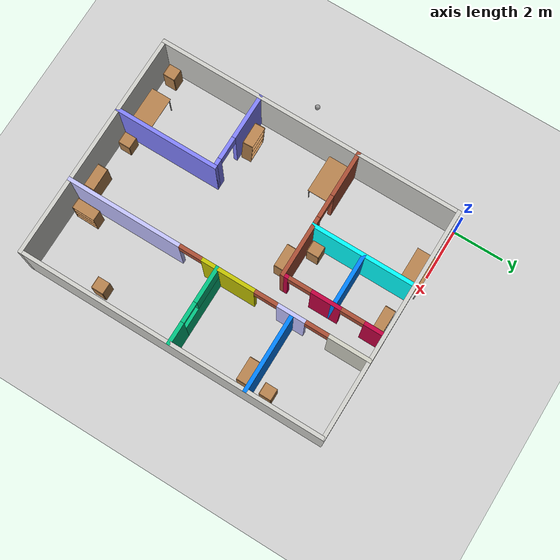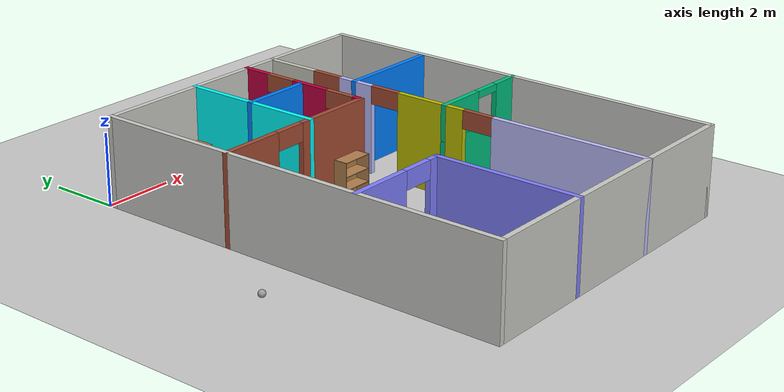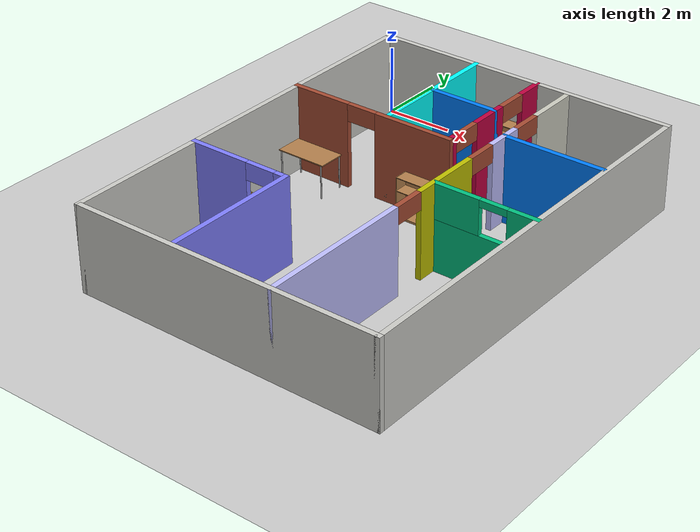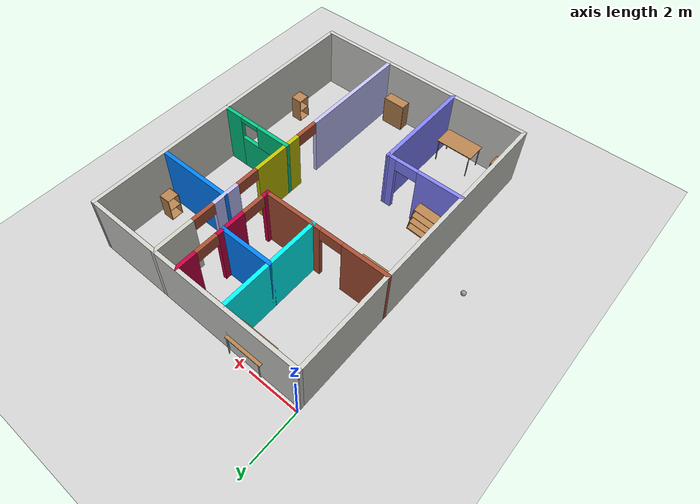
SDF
<sdf version="1.6">
 <world name="default">
  <plugin name="hello" filename="libhello.so"/>
  <light name="sun" type="directional">
   <pose>0 0 10 0 -0 0</pose>
   <diffuse>0.8 0.8 0.8 1</diffuse>
   <specular>0.2 0.2 0.2 1</specular>
   <attenuation>
    <range>1000</range>
    <constant>0.9</constant>
    <linear>0.01</linear>
    <quadratic>0.001</quadratic>
   </attenuation>
   <direction>-0.5 0.1 -0.9</direction>
  </light>
  <model name="ground_plane">
   <static>1</static>
   <link name="link">
    <collision name="collision">
     <geometry><plane><normal>0 0 1</normal><size>100 100</size></plane></geometry>
     <surface>
      <contact><collide_bitmask>65535</collide_bitmask></contact>
      <friction><ode><mu>100</mu><mu2>50</mu2></ode></friction>
     </surface>
    </collision>
    <visual name="visual">
     <cast_shadows>0</cast_shadows>
     <geometry><plane><normal>0 0 1</normal><size>100 100</size></plane></geometry>
     <material>
      <script><uri>file://media/materials/scripts/gazebo.material</uri><name>Gazebo/Grey</name></script>
     </material>
    </visual>
   </link>
  </model>
  <gravity>0 0 -9.8</gravity>
  <magnetic_field>6e-06 2.3e-05 -4.2e-05</magnetic_field>
  <atmosphere type="adiabatic"/>
  <physics name="default_physics" default="0" type="ode">
   <max_step_size>0.001</max_step_size>
   <real_time_factor>1</real_time_factor>
   <real_time_update_rate>1000</real_time_update_rate>
  </physics>
  <scene><ambient>0.4 0.4 0.4 1</ambient><background>0.7 0.7 0.7 1</background><shadows>1</shadows></scene>
  <spherical_coordinates>
   <surface_model>EARTH_WGS84</surface_model>
   <latitude_deg>0</latitude_deg>
   <longitude_deg>0</longitude_deg>
   <elevation>0</elevation>
   <heading_deg>0</heading_deg>
  </spherical_coordinates>
  <model name="table">
   <static>1</static>
   <link name="link">
    <collision name="surface">
     <pose>0 0 1 0 -0 0</pose>
     <geometry><box><size>1.5 0.8 0.03</size></box></geometry>
     <surface><friction><ode><mu>0.6</mu><mu2>0.6</mu2></ode></friction></surface>
    </collision>
    <visual name="visual1">
     <pose>0 0 1 0 -0 0</pose>
     <geometry><box><size>1.5 0.8 0.03</size></box></geometry>
     <material>
      <script><uri>file://media/materials/scripts/gazebo.material</uri><name>Gazebo/Wood</name></script>
     </material>
    </visual>
    <collision name="front_left_leg">
     <pose>0.68 0.38 0.5 0 -0 0</pose>
     <geometry><cylinder><radius>0.02</radius><length>1</length></cylinder></geometry>
    </collision>
    <visual name="front_left_leg">
     <pose>0.68 0.38 0.5 0 -0 0</pose>
     <geometry><cylinder><radius>0.02</radius><length>1</length></cylinder></geometry>
     <material>
      <script><uri>file://media/materials/scripts/gazebo.material</uri><name>Gazebo/Grey</name></script>
     </material>
    </visual>
    <collision name="front_right_leg">
     <pose>0.68 -0.38 0.5 0 -0 0</pose>
     <geometry><cylinder><radius>0.02</radius><length>1</length></cylinder></geometry>
    </collision>
    <visual name="front_right_leg">
     <pose>0.68 -0.38 0.5 0 -0 0</pose>
     <geometry><cylinder><radius>0.02</radius><length>1</length></cylinder></geometry>
     <material>
      <script><uri>file://media/materials/scripts/gazebo.material</uri><name>Gazebo/Grey</name></script>
     </material>
    </visual>
    <collision name="back_right_leg">
     <pose>-0.68 -0.38 0.5 0 -0 0</pose>
     <geometry><cylinder><radius>0.02</radius><length>1</length></cylinder></geometry>
    </collision>
    <visual name="back_right_leg">
     <pose>-0.68 -0.38 0.5 0 -0 0</pose>
     <geometry><cylinder><radius>0.02</radius><length>1</length></cylinder></geometry>
     <material>
      <script><uri>file://media/materials/scripts/gazebo.material</uri><name>Gazebo/Grey</name></script>
     </material>
    </visual>
    <collision name="back_left_leg">
     <pose>-0.68 0.38 0.5 0 -0 0</pose>
     <geometry><cylinder><radius>0.02</radius><length>1</length></cylinder></geometry>
    </collision>
    <visual name="back_left_leg">
     <pose>-0.68 0.38 0.5 0 -0 0</pose>
     <geometry><cylinder><radius>0.02</radius><length>1</length></cylinder></geometry>
     <material>
      <script><uri>file://media/materials/scripts/gazebo.material</uri><name>Gazebo/Grey</name></script>
     </material>
    </visual>
   </link>
   <pose>2.22125 -0.403374 0 0 -0 0</pose>
  </model>
  <model name="table_0">
   <static>1</static>
   <link name="link">
    <collision name="surface">
     <pose>0 0 1 0 -0 0</pose>
     <geometry><box><size>1.5 0.8 0.03</size></box></geometry>
     <surface><friction><ode><mu>0.6</mu><mu2>0.6</mu2></ode></friction></surface>
    </collision>
    <visual name="visual1">
     <pose>0 0 1 0 -0 0</pose>
     <geometry><box><size>1.5 0.8 0.03</size></box></geometry>
     <material>
      <script><uri>file://media/materials/scripts/gazebo.material</uri><name>Gazebo/Wood</name></script>
     </material>
    </visual>
    <collision name="front_left_leg">
     <pose>0.68 0.38 0.5 0 -0 0</pose>
     <geometry><cylinder><radius>0.02</radius><length>1</length></cylinder></geometry>
    </collision>
    <visual name="front_left_leg">
     <pose>0.68 0.38 0.5 0 -0 0</pose>
     <geometry><cylinder><radius>0.02</radius><length>1</length></cylinder></geometry>
     <material>
      <script><uri>file://media/materials/scripts/gazebo.material</uri><name>Gazebo/Grey</name></script>
     </material>
    </visual>
    <collision name="front_right_leg">
     <pose>0.68 -0.38 0.5 0 -0 0</pose>
     <geometry><cylinder><radius>0.02</radius><length>1</length></cylinder></geometry>
    </collision>
    <visual name="front_right_leg">
     <pose>0.68 -0.38 0.5 0 -0 0</pose>
     <geometry><cylinder><radius>0.02</radius><length>1</length></cylinder></geometry>
     <material>
      <script><uri>file://media/materials/scripts/gazebo.material</uri><name>Gazebo/Grey</name></script>
     </material>
    </visual>
    <collision name="back_right_leg">
     <pose>-0.68 -0.38 0.5 0 -0 0</pose>
     <geometry><cylinder><radius>0.02</radius><length>1</length></cylinder></geometry>
    </collision>
    <visual name="back_right_leg">
     <pose>-0.68 -0.38 0.5 0 -0 0</pose>
     <geometry><cylinder><radius>0.02</radius><length>1</length></cylinder></geometry>
     <material>
      <script><uri>file://media/materials/scripts/gazebo.material</uri><name>Gazebo/Grey</name></script>
     </material>
    </visual>
    <collision name="back_left_leg">
     <pose>-0.68 0.38 0.5 0 -0 0</pose>
     <geometry><cylinder><radius>0.02</radius><length>1</length></cylinder></geometry>
    </collision>
    <visual name="back_left_leg">
     <pose>-0.68 0.38 0.5 0 -0 0</pose>
     <geometry><cylinder><radius>0.02</radius><length>1</length></cylinder></geometry>
     <material>
      <script><uri>file://media/materials/scripts/gazebo.material</uri><name>Gazebo/Grey</name></script>
     </material>
    </visual>
   </link>
   <pose>2.11697 -11.6324 0 0 -0 0</pose>
  </model>
  <model name="my_ball">
   <link name="link">
    <inertial>
     <mass>1</mass>
     <inertia><ixx>0.1</ixx><ixy>0</ixy><ixz>0</ixz><iyy>0.1</iyy><iyz>0</iyz><izz>0.1</izz></inertia>
    </inertial>
    <visual name="visual">
     <geometry><sphere><radius>0.1</radius></sphere></geometry>
     <material>
      <script><name>Gazebo/Grey</name><uri>file://media/materials/scripts/gazebo.material</uri></script>
      <shader type="pixel"><normal_map>__default__</normal_map></shader>
      <ambient>1 1 1 1</ambient>
      <diffuse>1 1 1 1</diffuse>
      <specular>1 1 1 1</specular>
      <emissive>0 0 0 1</emissive>
     </material>
    </visual>
    <collision name="collision">
     <geometry><sphere><radius>0.1</radius></sphere></geometry>
     <surface>
      <friction>
       <ode><mu>1</mu><mu2>1</mu2><fdir1>0 0 0</fdir1><slip1>0</slip1><slip2>0</slip2></ode>
       <torsional>
        <coefficient>1</coefficient>
        <patch_radius>0</patch_radius>
        <surface_radius>0</surface_radius>
        <use_patch_radius>1</use_patch_radius>
        <ode><slip>0</slip></ode>
       </torsional>
      </friction>
      <bounce><restitution_coefficient>0</restitution_coefficient><threshold>1e+06</threshold></bounce>
      <contact>
       <collide_without_contact>0</collide_without_contact>
       <collide_without_contact_bitmask>1</collide_without_contact_bitmask>
       <collide_bitmask>1</collide_bitmask>
       <ode>
        <soft_cfm>0</soft_cfm>
        <soft_erp>0.2</soft_erp>
        <kp>1e+13</kp>
        <kd>1</kd>
        <max_vel>0.01</max_vel>
        <min_depth>0</min_depth>
       </ode>
       <bullet>
        <split_impulse>1</split_impulse>
        <split_impulse_penetration_threshold>-0.01</split_impulse_penetration_threshold>
        <soft_cfm>0</soft_cfm>
        <soft_erp>0.2</soft_erp>
        <kp>1e+13</kp>
        <kd>1</kd>
       </bullet>
      </contact>
     </surface>
    </collision>
   </link>
   <static>0</static>
   <pose>-1.47912 -6.67289 0.1 -2e-06 -0.020526 0</pose>
  </model>
  <model name="bookshelf">
   <static>1</static>
   <link name="link">
    <inertial><mass>1</mass></inertial>
    <collision name="back">
     <pose>0 0.005 0.6 0 -0 0</pose>
     <geometry><box><size>0.9 0.01 1.2</size></box></geometry>
    </collision>
    <visual name="visual1">
     <pose>0 0.005 0.6 0 -0 0</pose>
     <geometry><box><size>0.9 0.01 1.2</size></box></geometry>
     <material>
      <script><uri>file://media/materials/scripts/gazebo.material</uri><name>Gazebo/Wood</name></script>
     </material>
    </visual>
    <collision name="left_side">
     <pose>0.45 -0.195 0.6 0 -0 0</pose>
     <geometry><box><size>0.02 0.4 1.2</size></box></geometry>
    </collision>
    <visual name="visual2">
     <pose>0.45 -0.195 0.6 0 -0 0</pose>
     <geometry><box><size>0.02 0.4 1.2</size></box></geometry>
     <material>
      <script><uri>file://media/materials/scripts/gazebo.material</uri><name>Gazebo/Wood</name></script>
     </material>
    </visual>
    <collision name="right_side">
     <pose>-0.45 -0.195 0.6 0 -0 0</pose>
     <geometry><box><size>0.02 0.4 1.2</size></box></geometry>
    </collision>
    <visual name="visual3">
     <pose>-0.45 -0.195 0.6 0 -0 0</pose>
     <geometry><box><size>0.02 0.4 1.2</size></box></geometry>
     <material>
      <script><uri>file://media/materials/scripts/gazebo.material</uri><name>Gazebo/Wood</name></script>
     </material>
    </visual>
    <collision name="bottom">
     <pose>0 -0.195 0.03 0 -0 0</pose>
     <geometry><box><size>0.88 0.4 0.06</size></box></geometry>
    </collision>
    <visual name="visual4">
     <pose>0 -0.195 0.03 0 -0 0</pose>
     <geometry><box><size>0.88 0.4 0.06</size></box></geometry>
     <material>
      <script><uri>file://media/materials/scripts/gazebo.material</uri><name>Gazebo/Wood</name></script>
     </material>
    </visual>
    <collision name="top">
     <pose>0 -0.195 1.19 0 -0 0</pose>
     <geometry><box><size>0.88 0.4 0.02</size></box></geometry>
    </collision>
    <visual name="visual5">
     <pose>0 -0.195 1.19 0 -0 0</pose>
     <geometry><box><size>0.88 0.4 0.02</size></box></geometry>
     <material>
      <script><uri>file://media/materials/scripts/gazebo.material</uri><name>Gazebo/Wood</name></script>
     </material>
    </visual>
    <collision name="low_shelf">
     <pose>0 -0.195 0.43 0 -0 0</pose>
     <geometry><box><size>0.88 0.4 0.02</size></box></geometry>
    </collision>
    <visual name="visual6">
     <pose>0 -0.195 0.43 0 -0 0</pose>
     <geometry><box><size>0.88 0.4 0.02</size></box></geometry>
     <material>
      <script><uri>file://media/materials/scripts/gazebo.material</uri><name>Gazebo/Wood</name></script>
     </material>
    </visual>
    <collision name="high_shelf">
     <pose>0 -0.195 0.8 0 -0 0</pose>
     <geometry><box><size>0.88 0.4 0.02</size></box></geometry>
    </collision>
    <visual name="visual7">
     <pose>0 -0.195 0.8 0 -0 0</pose>
     <geometry><box><size>0.88 0.4 0.02</size></box></geometry>
     <material>
      <script><uri>file://media/materials/scripts/gazebo.material</uri><name>Gazebo/Wood</name></script>
     </material>
    </visual>
   </link>
   <pose>5.28995 -11.6581 0 0 -0 0</pose>
  </model>
  <model name="cabinet">
   <static>1</static>
   <link name="cabinet_bottom_plate">
    <inertial>
     <pose>0 0 -1 0 -0 0</pose>
     <inertia><ixx>2.05</ixx><ixy>0</ixy><ixz>0</ixz><iyy>2.05</iyy><iyz>0</iyz><izz>2.05</izz></inertia>
     <mass>25</mass>
    </inertial>
    <collision name="cabinet_bottom_plate_geom">
     <pose>0 0 0.01 0 -0 0</pose>
     <geometry><box><size>0.45 0.45 0.02</size></box></geometry>
    </collision>
    <visual name="cabinet_bottom_plate_geom_visual">
     <pose>0 0 0.01 0 -0 0</pose>
     <geometry><box><size>0.45 0.45 0.02</size></box></geometry>
     <material>
      <script><uri>file://media/materials/scripts/gazebo.material</uri><name>Gazebo/Wood</name></script>
     </material>
    </visual>
    <collision name="cabinet_bottom_plate_geom_cabinet_back_plate">
     <pose>0.235 0 0.51 0 -0 0</pose>
     <geometry><box><size>0.02 0.45 1.02</size></box></geometry>
    </collision>
    <visual name="cabinet_bottom_plate_geom_cabinet_back_plate_visual">
     <pose>0.235 0 0.51 0 -0 0</pose>
     <geometry><box><size>0.02 0.45 1.02</size></box></geometry>
     <material>
      <script><uri>file://media/materials/scripts/gazebo.material</uri><name>Gazebo/Wood</name></script>
     </material>
    </visual>
    <collision name="cabinet_bottom_plate_geom_cabinet_left_plate">
     <pose>0 0.235 0.51 0 -0 0</pose>
     <geometry><box><size>0.45 0.02 1.02</size></box></geometry>
    </collision>
    <visual name="cabinet_bottom_plate_geom_cabinet_left_plate_visual">
     <pose>0 0.235 0.51 0 -0 0</pose>
     <geometry><box><size>0.45 0.02 1.02</size></box></geometry>
     <material>
      <script><uri>file://media/materials/scripts/gazebo.material</uri><name>Gazebo/Wood</name></script>
     </material>
    </visual>
    <collision name="cabinet_bottom_plate_geom_cabinet_middle_plate">
     <pose>0 0 0.51 0 -0 0</pose>
     <geometry><box><size>0.45 0.45 0.02</size></box></geometry>
    </collision>
    <visual name="cabinet_bottom_plate_geom_cabinet_middle_plate_visual">
     <pose>0 0 0.51 0 -0 0</pose>
     <geometry><box><size>0.45 0.45 0.02</size></box></geometry>
     <material>
      <script><uri>file://media/materials/scripts/gazebo.material</uri><name>Gazebo/Wood</name></script>
     </material>
    </visual>
    <collision name="cabinet_bottom_plate_geom_cabinet_right_plate">
     <pose>0 -0.235 0.51 0 -0 0</pose>
     <geometry><box><size>0.45 0.02 1.02</size></box></geometry>
    </collision>
    <visual name="cabinet_bottom_plate_geom_cabinet_right_plate_visual">
     <pose>0 -0.235 0.51 0 -0 0</pose>
     <geometry><box><size>0.45 0.02 1.02</size></box></geometry>
     <material>
      <script><uri>file://media/materials/scripts/gazebo.material</uri><name>Gazebo/Wood</name></script>
     </material>
    </visual>
    <collision name="cabinet_bottom_plate_geom_cabinet_top_plate">
     <pose>0 0 1.01 0 -0 0</pose>
     <geometry><box><size>0.45 0.45 0.02</size></box></geometry>
    </collision>
    <visual name="cabinet_bottom_plate_geom_cabinet_top_plate_visual">
     <pose>0 0 1.01 0 -0 0</pose>
     <geometry><box><size>0.45 0.45 0.02</size></box></geometry>
     <material>
      <script><uri>file://media/materials/scripts/gazebo.material</uri><name>Gazebo/Wood</name></script>
     </material>
    </visual>
   </link>
   <pose>0.457924 -11.7568 0 0 -0 0</pose>
  </model>
  <model name="cabinet_0">
   <static>1</static>
   <link name="cabinet_bottom_plate">
    <inertial>
     <pose>0 0 -1 0 -0 0</pose>
     <inertia><ixx>2.05</ixx><ixy>0</ixy><ixz>0</ixz><iyy>2.05</iyy><iyz>0</iyz><izz>2.05</izz></inertia>
     <mass>25</mass>
    </inertial>
    <collision name="cabinet_bottom_plate_geom">
     <pose>0 0 0.01 0 -0 0</pose>
     <geometry><box><size>0.45 0.45 0.02</size></box></geometry>
    </collision>
    <visual name="cabinet_bottom_plate_geom_visual">
     <pose>0 0 0.01 0 -0 0</pose>
     <geometry><box><size>0.45 0.45 0.02</size></box></geometry>
     <material>
      <script><uri>file://media/materials/scripts/gazebo.material</uri><name>Gazebo/Wood</name></script>
     </material>
    </visual>
    <collision name="cabinet_bottom_plate_geom_cabinet_back_plate">
     <pose>0.235 0 0.51 0 -0 0</pose>
     <geometry><box><size>0.02 0.45 1.02</size></box></geometry>
    </collision>
    <visual name="cabinet_bottom_plate_geom_cabinet_back_plate_visual">
     <pose>0.235 0 0.51 0 -0 0</pose>
     <geometry><box><size>0.02 0.45 1.02</size></box></geometry>
     <material>
      <script><uri>file://media/materials/scripts/gazebo.material</uri><name>Gazebo/Wood</name></script>
     </material>
    </visual>
    <collision name="cabinet_bottom_plate_geom_cabinet_left_plate">
     <pose>0 0.235 0.51 0 -0 0</pose>
     <geometry><box><size>0.45 0.02 1.02</size></box></geometry>
    </collision>
    <visual name="cabinet_bottom_plate_geom_cabinet_left_plate_visual">
     <pose>0 0.235 0.51 0 -0 0</pose>
     <geometry><box><size>0.45 0.02 1.02</size></box></geometry>
     <material>
      <script><uri>file://media/materials/scripts/gazebo.material</uri><name>Gazebo/Wood</name></script>
     </material>
    </visual>
    <collision name="cabinet_bottom_plate_geom_cabinet_middle_plate">
     <pose>0 0 0.51 0 -0 0</pose>
     <geometry><box><size>0.45 0.45 0.02</size></box></geometry>
    </collision>
    <visual name="cabinet_bottom_plate_geom_cabinet_middle_plate_visual">
     <pose>0 0 0.51 0 -0 0</pose>
     <geometry><box><size>0.45 0.45 0.02</size></box></geometry>
     <material>
      <script><uri>file://media/materials/scripts/gazebo.material</uri><name>Gazebo/Wood</name></script>
     </material>
    </visual>
    <collision name="cabinet_bottom_plate_geom_cabinet_right_plate">
     <pose>0 -0.235 0.51 0 -0 0</pose>
     <geometry><box><size>0.45 0.02 1.02</size></box></geometry>
    </collision>
    <visual name="cabinet_bottom_plate_geom_cabinet_right_plate_visual">
     <pose>0 -0.235 0.51 0 -0 0</pose>
     <geometry><box><size>0.45 0.02 1.02</size></box></geometry>
     <material>
      <script><uri>file://media/materials/scripts/gazebo.material</uri><name>Gazebo/Wood</name></script>
     </material>
    </visual>
    <collision name="cabinet_bottom_plate_geom_cabinet_top_plate">
     <pose>0 0 1.01 0 -0 0</pose>
     <geometry><box><size>0.45 0.45 0.02</size></box></geometry>
    </collision>
    <visual name="cabinet_bottom_plate_geom_cabinet_top_plate_visual">
     <pose>0 0 1.01 0 -0 0</pose>
     <geometry><box><size>0.45 0.45 0.02</size></box></geometry>
     <material>
      <script><uri>file://media/materials/scripts/gazebo.material</uri><name>Gazebo/Wood</name></script>
     </material>
    </visual>
   </link>
   <pose>8.53968 -2.63163 0 0 -0 0</pose>
  </model>
  <model name="cabinet_1">
   <static>1</static>
   <link name="cabinet_bottom_plate">
    <inertial>
     <pose>0 0 -1 0 -0 0</pose>
     <inertia><ixx>2.05</ixx><ixy>0</ixy><ixz>0</ixz><iyy>2.05</iyy><iyz>0</iyz><izz>2.05</izz></inertia>
     <mass>25</mass>
    </inertial>
    <collision name="cabinet_bottom_plate_geom">
     <pose>0 0 0.01 0 -0 0</pose>
     <geometry><box><size>0.45 0.45 0.02</size></box></geometry>
    </collision>
    <visual name="cabinet_bottom_plate_geom_visual">
     <pose>0 0 0.01 0 -0 0</pose>
     <geometry><box><size>0.45 0.45 0.02</size></box></geometry>
     <material>
      <script><uri>file://media/materials/scripts/gazebo.material</uri><name>Gazebo/Wood</name></script>
     </material>
    </visual>
    <collision name="cabinet_bottom_plate_geom_cabinet_back_plate">
     <pose>0.235 0 0.51 0 -0 0</pose>
     <geometry><box><size>0.02 0.45 1.02</size></box></geometry>
    </collision>
    <visual name="cabinet_bottom_plate_geom_cabinet_back_plate_visual">
     <pose>0.235 0 0.51 0 -0 0</pose>
     <geometry><box><size>0.02 0.45 1.02</size></box></geometry>
     <material>
      <script><uri>file://media/materials/scripts/gazebo.material</uri><name>Gazebo/Wood</name></script>
     </material>
    </visual>
    <collision name="cabinet_bottom_plate_geom_cabinet_left_plate">
     <pose>0 0.235 0.51 0 -0 0</pose>
     <geometry><box><size>0.45 0.02 1.02</size></box></geometry>
    </collision>
    <visual name="cabinet_bottom_plate_geom_cabinet_left_plate_visual">
     <pose>0 0.235 0.51 0 -0 0</pose>
     <geometry><box><size>0.45 0.02 1.02</size></box></geometry>
     <material>
      <script><uri>file://media/materials/scripts/gazebo.material</uri><name>Gazebo/Wood</name></script>
     </material>
    </visual>
    <collision name="cabinet_bottom_plate_geom_cabinet_middle_plate">
     <pose>0 0 0.51 0 -0 0</pose>
     <geometry><box><size>0.45 0.45 0.02</size></box></geometry>
    </collision>
    <visual name="cabinet_bottom_plate_geom_cabinet_middle_plate_visual">
     <pose>0 0 0.51 0 -0 0</pose>
     <geometry><box><size>0.45 0.45 0.02</size></box></geometry>
     <material>
      <script><uri>file://media/materials/scripts/gazebo.material</uri><name>Gazebo/Wood</name></script>
     </material>
    </visual>
    <collision name="cabinet_bottom_plate_geom_cabinet_right_plate">
     <pose>0 -0.235 0.51 0 -0 0</pose>
     <geometry><box><size>0.45 0.02 1.02</size></box></geometry>
    </collision>
    <visual name="cabinet_bottom_plate_geom_cabinet_right_plate_visual">
     <pose>0 -0.235 0.51 0 -0 0</pose>
     <geometry><box><size>0.45 0.02 1.02</size></box></geometry>
     <material>
      <script><uri>file://media/materials/scripts/gazebo.material</uri><name>Gazebo/Wood</name></script>
     </material>
    </visual>
    <collision name="cabinet_bottom_plate_geom_cabinet_top_plate">
     <pose>0 0 1.01 0 -0 0</pose>
     <geometry><box><size>0.45 0.45 0.02</size></box></geometry>
    </collision>
    <visual name="cabinet_bottom_plate_geom_cabinet_top_plate_visual">
     <pose>0 0 1.01 0 -0 0</pose>
     <geometry><box><size>0.45 0.45 0.02</size></box></geometry>
     <material>
      <script><uri>file://media/materials/scripts/gazebo.material</uri><name>Gazebo/Wood</name></script>
     </material>
    </visual>
   </link>
   <pose>3.39674 -3.83309 0 0 -0 0</pose>
  </model>
  <model name="table_1">
   <static>1</static>
   <link name="link">
    <collision name="surface">
     <pose>0 0 1 0 -0 0</pose>
     <geometry><box><size>1.5 0.8 0.03</size></box></geometry>
     <surface><friction><ode><mu>0.6</mu><mu2>0.6</mu2></ode></friction></surface>
    </collision>
    <visual name="visual1">
     <pose>0 0 1 0 -0 0</pose>
     <geometry><box><size>1.5 0.8 0.03</size></box></geometry>
     <material>
      <script><uri>file://media/materials/scripts/gazebo.material</uri><name>Gazebo/Wood</name></script>
     </material>
    </visual>
    <collision name="front_left_leg">
     <pose>0.68 0.38 0.5 0 -0 0</pose>
     <geometry><cylinder><radius>0.02</radius><length>1</length></cylinder></geometry>
    </collision>
    <visual name="front_left_leg">
     <pose>0.68 0.38 0.5 0 -0 0</pose>
     <geometry><cylinder><radius>0.02</radius><length>1</length></cylinder></geometry>
     <material>
      <script><uri>file://media/materials/scripts/gazebo.material</uri><name>Gazebo/Grey</name></script>
     </material>
    </visual>
    <collision name="front_right_leg">
     <pose>0.68 -0.38 0.5 0 -0 0</pose>
     <geometry><cylinder><radius>0.02</radius><length>1</length></cylinder></geometry>
    </collision>
    <visual name="front_right_leg">
     <pose>0.68 -0.38 0.5 0 -0 0</pose>
     <geometry><cylinder><radius>0.02</radius><length>1</length></cylinder></geometry>
     <material>
      <script><uri>file://media/materials/scripts/gazebo.material</uri><name>Gazebo/Grey</name></script>
     </material>
    </visual>
    <collision name="back_right_leg">
     <pose>-0.68 -0.38 0.5 0 -0 0</pose>
     <geometry><cylinder><radius>0.02</radius><length>1</length></cylinder></geometry>
    </collision>
    <visual name="back_right_leg">
     <pose>-0.68 -0.38 0.5 0 -0 0</pose>
     <geometry><cylinder><radius>0.02</radius><length>1</length></cylinder></geometry>
     <material>
      <script><uri>file://media/materials/scripts/gazebo.material</uri><name>Gazebo/Grey</name></script>
     </material>
    </visual>
    <collision name="back_left_leg">
     <pose>-0.68 0.38 0.5 0 -0 0</pose>
     <geometry><cylinder><radius>0.02</radius><length>1</length></cylinder></geometry>
    </collision>
    <visual name="back_left_leg">
     <pose>-0.68 0.38 0.5 0 -0 0</pose>
     <geometry><cylinder><radius>0.02</radius><length>1</length></cylinder></geometry>
     <material>
      <script><uri>file://media/materials/scripts/gazebo.material</uri><name>Gazebo/Grey</name></script>
     </material>
    </visual>
   </link>
   <pose>0.950805 -4.79839 0 0 0 -0.003535</pose>
  </model>
  <model name="my_building">
   <link name="Wall_0">
    <pose>0 6 0 0 -0 0</pose>
    <visual name="Wall_0_Visual">
     <pose>0 0 1.25 0 -0 0</pose>
     <geometry><box><size>9.15 0.15 2.5</size></box></geometry>
     <material>
      <script><uri>file://media/materials/scripts/gazebo.material</uri><name>Gazebo/CeilingTiled</name></script>
      <ambient>0.760784 0.662745 0.627451 1</ambient>
      <shader type="pixel"/>
      <diffuse>1 1 1 1</diffuse>
      <specular>0 0 0 1</specular>
      <emissive>0 0 0 1</emissive>
     </material>
     <meta><layer>0</layer></meta>
    </visual>
    <collision name="Wall_0_Collision">
     <pose>0 0 1.25 0 -0 0</pose>
     <geometry><box><size>9.15 0.15 2.5</size></box></geometry>
     <surface>
      <friction>
       <ode><mu>1</mu><mu2>1</mu2><fdir1>0 0 0</fdir1><slip1>0</slip1><slip2>0</slip2></ode>
       <torsional>
        <coefficient>1</coefficient>
        <patch_radius>0</patch_radius>
        <surface_radius>0</surface_radius>
        <use_patch_radius>1</use_patch_radius>
        <ode><slip>0</slip></ode>
       </torsional>
      </friction>
      <bounce><restitution_coefficient>0</restitution_coefficient><threshold>1e+06</threshold></bounce>
      <contact>
       <collide_without_contact>0</collide_without_contact>
       <collide_without_contact_bitmask>1</collide_without_contact_bitmask>
       <collide_bitmask>1</collide_bitmask>
       <ode>
        <soft_cfm>0</soft_cfm>
        <soft_erp>0.2</soft_erp>
        <kp>1e+13</kp>
        <kd>1</kd>
        <max_vel>0.01</max_vel>
        <min_depth>0</min_depth>
       </ode>
       <bullet>
        <split_impulse>1</split_impulse>
        <split_impulse_penetration_threshold>-0.01</split_impulse_penetration_threshold>
        <soft_cfm>0</soft_cfm>
        <soft_erp>0.2</soft_erp>
        <kp>1e+13</kp>
        <kd>1</kd>
       </bullet>
      </contact>
     </surface>
    </collision>
   </link>
   <link name="Wall_11">
    <pose>-1.5 4 0 0 0 -1.5708</pose>
    <inertial>
     <mass>1</mass>
     <inertia><ixx>1</ixx><ixy>0</ixy><ixz>0</ixz><iyy>1</iyy><iyz>0</iyz><izz>1</izz></inertia>
    </inertial>
    <visual name="Wall_11_Visual">
     <pose>0 0 1.25 0 -0 0</pose>
     <geometry><box><size>4.15 0.15 2.5</size></box></geometry>
     <material>
      <script><uri>file://media/materials/scripts/gazebo.material</uri><name>Gazebo/Grey</name></script>
      <ambient>0 1 1 1</ambient>
      <shader type="pixel"><normal_map>__default__</normal_map></shader>
      <diffuse>0.7 0.7 0.7 1</diffuse>
      <specular>0.01 0.01 0.01 1</specular>
      <emissive>0 0 0 1</emissive>
     </material>
     <meta><layer>0</layer></meta>
    </visual>
    <collision name="Wall_11_Collision">
     <pose>0 0 1.25 0 -0 0</pose>
     <geometry><box><size>4.15 0.15 2.5</size></box></geometry>
     <surface>
      <friction>
       <ode><mu>1</mu><mu2>1</mu2><fdir1>0 0 0</fdir1><slip1>0</slip1><slip2>0</slip2></ode>
       <torsional>
        <coefficient>1</coefficient>
        <patch_radius>0</patch_radius>
        <surface_radius>0</surface_radius>
        <use_patch_radius>1</use_patch_radius>
        <ode><slip>0</slip></ode>
       </torsional>
      </friction>
      <bounce><restitution_coefficient>0</restitution_coefficient><threshold>1e+06</threshold></bounce>
      <contact>
       <collide_without_contact>0</collide_without_contact>
       <collide_without_contact_bitmask>1</collide_without_contact_bitmask>
       <collide_bitmask>1</collide_bitmask>
       <ode>
        <soft_cfm>0</soft_cfm>
        <soft_erp>0.2</soft_erp>
        <kp>1e+13</kp>
        <kd>1</kd>
        <max_vel>0.01</max_vel>
        <min_depth>0</min_depth>
       </ode>
       <bullet>
        <split_impulse>1</split_impulse>
        <split_impulse_penetration_threshold>-0.01</split_impulse_penetration_threshold>
        <soft_cfm>0</soft_cfm>
        <soft_erp>0.2</soft_erp>
        <kp>1e+13</kp>
        <kd>1</kd>
       </bullet>
      </contact>
     </surface>
    </collision>
   </link>
   <link name="Wall_13">
    <pose>-2 2 0 0 -0 0</pose>
    <inertial>
     <mass>1</mass>
     <inertia><ixx>1</ixx><ixy>0</ixy><ixz>0</ixz><iyy>1</iyy><iyz>0</iyz><izz>1</izz></inertia>
    </inertial>
    <visual name="Wall_13_Visual_2">
     <pose>-0.287034 0 2.25 0 -0 0</pose>
     <geometry><box><size>0.9 0.15 0.5</size></box></geometry>
     <material>
      <script><uri>file://media/materials/scripts/gazebo.material</uri><name>Gazebo/Bricks</name></script>
      <ambient>1 1 1 1</ambient>
      <shader type="pixel"><normal_map>__default__</normal_map></shader>
      <diffuse>0.7 0.7 0.7 1</diffuse>
      <specular>0.01 0.01 0.01 1</specular>
      <emissive>0 0 0 1</emissive>
     </material>
     <meta><layer>0</layer></meta>
    </visual>
    <visual name="Wall_13_Visual_0">
     <pose>-1.65602 0 1.25 0 -0 0</pose>
     <geometry><box><size>1.83797 0.15 2.5</size></box></geometry>
     <material>
      <script><uri>file://media/materials/scripts/gazebo.material</uri><name>Gazebo/Bricks</name></script>
      <ambient>1 1 1 1</ambient>
      <shader type="pixel"><normal_map>__default__</normal_map></shader>
      <diffuse>0.7 0.7 0.7 1</diffuse>
      <specular>0.01 0.01 0.01 1</specular>
      <emissive>0 0 0 1</emissive>
     </material>
     <meta><layer>0</layer></meta>
    </visual>
    <visual name="Wall_13_Visual_1">
     <pose>1.36898 0 1.25 0 -0 0</pose>
     <geometry><box><size>2.41203 0.15 2.5</size></box></geometry>
     <material>
      <script><uri>file://media/materials/scripts/gazebo.material</uri><name>Gazebo/Bricks</name></script>
      <ambient>1 1 1 1</ambient>
      <shader type="pixel"><normal_map>__default__</normal_map></shader>
      <diffuse>0.7 0.7 0.7 1</diffuse>
      <specular>0.01 0.01 0.01 1</specular>
      <emissive>0 0 0 1</emissive>
     </material>
     <meta><layer>0</layer></meta>
    </visual>
    <collision name="Wall_13_Collision_1">
     <pose>1.36898 0 1.25 0 -0 0</pose>
     <geometry><box><size>2.41203 0.15 2.5</size></box></geometry>
     <surface>
      <friction>
       <ode><mu>1</mu><mu2>1</mu2><fdir1>0 0 0</fdir1><slip1>0</slip1><slip2>0</slip2></ode>
       <torsional>
        <coefficient>1</coefficient>
        <patch_radius>0</patch_radius>
        <surface_radius>0</surface_radius>
        <use_patch_radius>1</use_patch_radius>
        <ode><slip>0</slip></ode>
       </torsional>
      </friction>
      <bounce><restitution_coefficient>0</restitution_coefficient><threshold>1e+06</threshold></bounce>
      <contact>
       <collide_without_contact>0</collide_without_contact>
       <collide_without_contact_bitmask>1</collide_without_contact_bitmask>
       <collide_bitmask>1</collide_bitmask>
       <ode>
        <soft_cfm>0</soft_cfm>
        <soft_erp>0.2</soft_erp>
        <kp>1e+13</kp>
        <kd>1</kd>
        <max_vel>0.01</max_vel>
        <min_depth>0</min_depth>
       </ode>
       <bullet>
        <split_impulse>1</split_impulse>
        <split_impulse_penetration_threshold>-0.01</split_impulse_penetration_threshold>
        <soft_cfm>0</soft_cfm>
        <soft_erp>0.2</soft_erp>
        <kp>1e+13</kp>
        <kd>1</kd>
       </bullet>
      </contact>
     </surface>
    </collision>
    <collision name="Wall_13_Collision_0">
     <pose>-1.65602 0 1.25 0 -0 0</pose>
     <geometry><box><size>1.83797 0.15 2.5</size></box></geometry>
     <surface>
      <friction>
       <ode><mu>1</mu><mu2>1</mu2><fdir1>0 0 0</fdir1><slip1>0</slip1><slip2>0</slip2></ode>
       <torsional>
        <coefficient>1</coefficient>
        <patch_radius>0</patch_radius>
        <surface_radius>0</surface_radius>
        <use_patch_radius>1</use_patch_radius>
        <ode><slip>0</slip></ode>
       </torsional>
      </friction>
      <bounce><restitution_coefficient>0</restitution_coefficient><threshold>1e+06</threshold></bounce>
      <contact>
       <collide_without_contact>0</collide_without_contact>
       <collide_without_contact_bitmask>1</collide_without_contact_bitmask>
       <collide_bitmask>1</collide_bitmask>
       <ode>
        <soft_cfm>0</soft_cfm>
        <soft_erp>0.2</soft_erp>
        <kp>1e+13</kp>
        <kd>1</kd>
        <max_vel>0.01</max_vel>
        <min_depth>0</min_depth>
       </ode>
       <bullet>
        <split_impulse>1</split_impulse>
        <split_impulse_penetration_threshold>-0.01</split_impulse_penetration_threshold>
        <soft_cfm>0</soft_cfm>
        <soft_erp>0.2</soft_erp>
        <kp>1e+13</kp>
        <kd>1</kd>
       </bullet>
      </contact>
     </surface>
    </collision>
    <collision name="Wall_13_Collision_2">
     <pose>-0.287034 0 2.25 0 -0 0</pose>
     <geometry><box><size>0.9 0.15 0.5</size></box></geometry>
     <surface>
      <friction>
       <ode><mu>1</mu><mu2>1</mu2><fdir1>0 0 0</fdir1><slip1>0</slip1><slip2>0</slip2></ode>
       <torsional>
        <coefficient>1</coefficient>
        <patch_radius>0</patch_radius>
        <surface_radius>0</surface_radius>
        <use_patch_radius>1</use_patch_radius>
        <ode><slip>0</slip></ode>
       </torsional>
      </friction>
      <bounce><restitution_coefficient>0</restitution_coefficient><threshold>1e+06</threshold></bounce>
      <contact>
       <collide_without_contact>0</collide_without_contact>
       <collide_without_contact_bitmask>1</collide_without_contact_bitmask>
       <collide_bitmask>1</collide_bitmask>
       <ode>
        <soft_cfm>0</soft_cfm>
        <soft_erp>0.2</soft_erp>
        <kp>1e+13</kp>
        <kd>1</kd>
        <max_vel>0.01</max_vel>
        <min_depth>0</min_depth>
       </ode>
       <bullet>
        <split_impulse>1</split_impulse>
        <split_impulse_penetration_threshold>-0.01</split_impulse_penetration_threshold>
        <soft_cfm>0</soft_cfm>
        <soft_erp>0.2</soft_erp>
        <kp>1e+13</kp>
        <kd>1</kd>
       </bullet>
      </contact>
     </surface>
    </collision>
   </link>
   <link name="Wall_15">
    <pose>-3 -2 0 0 -0 0</pose>
    <inertial>
     <mass>1</mass>
     <inertia><ixx>1</ixx><ixy>0</ixy><ixz>0</ixz><iyy>1</iyy><iyz>0</iyz><izz>1</izz></inertia>
    </inertial>
    <visual name="Wall_15_Visual_0">
     <pose>-0.656017 0 1.25 0 -0 0</pose>
     <geometry><box><size>1.83797 0.15 2.5</size></box></geometry>
     <material>
      <script><uri>file://media/materials/scripts/gazebo.material</uri><name>Gazebo/Grey</name></script>
      <ambient>0.5 0.5 1 1</ambient>
      <shader type="pixel"><normal_map>__default__</normal_map></shader>
      <diffuse>0.7 0.7 0.7 1</diffuse>
      <specular>0.01 0.01 0.01 1</specular>
      <emissive>0 0 0 1</emissive>
     </material>
     <meta><layer>0</layer></meta>
    </visual>
    <visual name="Wall_15_Visual_1">
     <pose>1.36898 0 1.25 0 -0 0</pose>
     <geometry><box><size>0.412034 0.15 2.5</size></box></geometry>
     <material>
      <script><uri>file://media/materials/scripts/gazebo.material</uri><name>Gazebo/Grey</name></script>
      <ambient>0.5 0.5 1 1</ambient>
      <shader type="pixel"><normal_map>__default__</normal_map></shader>
      <diffuse>0.7 0.7 0.7 1</diffuse>
      <specular>0.01 0.01 0.01 1</specular>
      <emissive>0 0 0 1</emissive>
     </material>
     <meta><layer>0</layer></meta>
    </visual>
    <visual name="Wall_15_Visual_2">
     <pose>0.712966 0 2.25 0 -0 0</pose>
     <geometry><box><size>0.9 0.15 0.5</size></box></geometry>
     <material>
      <script><uri>file://media/materials/scripts/gazebo.material</uri><name>Gazebo/Grey</name></script>
      <ambient>0.5 0.5 1 1</ambient>
      <shader type="pixel"><normal_map>__default__</normal_map></shader>
      <diffuse>0.7 0.7 0.7 1</diffuse>
      <specular>0.01 0.01 0.01 1</specular>
      <emissive>0 0 0 1</emissive>
     </material>
     <meta><layer>0</layer></meta>
    </visual>
    <collision name="Wall_15_Collision_0">
     <pose>-0.656017 0 1.25 0 -0 0</pose>
     <geometry><box><size>1.83797 0.15 2.5</size></box></geometry>
     <surface>
      <friction>
       <ode><mu>1</mu><mu2>1</mu2><fdir1>0 0 0</fdir1><slip1>0</slip1><slip2>0</slip2></ode>
       <torsional>
        <coefficient>1</coefficient>
        <patch_radius>0</patch_radius>
        <surface_radius>0</surface_radius>
        <use_patch_radius>1</use_patch_radius>
        <ode><slip>0</slip></ode>
       </torsional>
      </friction>
      <bounce><restitution_coefficient>0</restitution_coefficient><threshold>1e+06</threshold></bounce>
      <contact>
       <collide_without_contact>0</collide_without_contact>
       <collide_without_contact_bitmask>1</collide_without_contact_bitmask>
       <collide_bitmask>1</collide_bitmask>
       <ode>
        <soft_cfm>0</soft_cfm>
        <soft_erp>0.2</soft_erp>
        <kp>1e+13</kp>
        <kd>1</kd>
        <max_vel>0.01</max_vel>
        <min_depth>0</min_depth>
       </ode>
       <bullet>
        <split_impulse>1</split_impulse>
        <split_impulse_penetration_threshold>-0.01</split_impulse_penetration_threshold>
        <soft_cfm>0</soft_cfm>
        <soft_erp>0.2</soft_erp>
        <kp>1e+13</kp>
        <kd>1</kd>
       </bullet>
      </contact>
     </surface>
    </collision>
    <collision name="Wall_15_Collision_2">
     <pose>0.712966 0 2.25 0 -0 0</pose>
     <geometry><box><size>0.9 0.15 0.5</size></box></geometry>
     <surface>
      <friction>
       <ode><mu>1</mu><mu2>1</mu2><fdir1>0 0 0</fdir1><slip1>0</slip1><slip2>0</slip2></ode>
       <torsional>
        <coefficient>1</coefficient>
        <patch_radius>0</patch_radius>
        <surface_radius>0</surface_radius>
        <use_patch_radius>1</use_patch_radius>
        <ode><slip>0</slip></ode>
       </torsional>
      </friction>
      <bounce><restitution_coefficient>0</restitution_coefficient><threshold>1e+06</threshold></bounce>
      <contact>
       <collide_without_contact>0</collide_without_contact>
       <collide_without_contact_bitmask>1</collide_without_contact_bitmask>
       <collide_bitmask>1</collide_bitmask>
       <ode>
        <soft_cfm>0</soft_cfm>
        <soft_erp>0.2</soft_erp>
        <kp>1e+13</kp>
        <kd>1</kd>
        <max_vel>0.01</max_vel>
        <min_depth>0</min_depth>
       </ode>
       <bullet>
        <split_impulse>1</split_impulse>
        <split_impulse_penetration_threshold>-0.01</split_impulse_penetration_threshold>
        <soft_cfm>0</soft_cfm>
        <soft_erp>0.2</soft_erp>
        <kp>1e+13</kp>
        <kd>1</kd>
       </bullet>
      </contact>
     </surface>
    </collision>
    <collision name="Wall_15_Collision_1">
     <pose>1.36898 0 1.25 0 -0 0</pose>
     <geometry><box><size>0.412034 0.15 2.5</size></box></geometry>
     <surface>
      <friction>
       <ode><mu>1</mu><mu2>1</mu2><fdir1>0 0 0</fdir1><slip1>0</slip1><slip2>0</slip2></ode>
       <torsional>
        <coefficient>1</coefficient>
        <patch_radius>0</patch_radius>
        <surface_radius>0</surface_radius>
        <use_patch_radius>1</use_patch_radius>
        <ode><slip>0</slip></ode>
       </torsional>
      </friction>
      <bounce><restitution_coefficient>0</restitution_coefficient><threshold>1e+06</threshold></bounce>
      <contact>
       <collide_without_contact>0</collide_without_contact>
       <collide_without_contact_bitmask>1</collide_without_contact_bitmask>
       <collide_bitmask>1</collide_bitmask>
       <ode>
        <soft_cfm>0</soft_cfm>
        <soft_erp>0.2</soft_erp>
        <kp>1e+13</kp>
        <kd>1</kd>
        <max_vel>0.01</max_vel>
        <min_depth>0</min_depth>
       </ode>
       <bullet>
        <split_impulse>1</split_impulse>
        <split_impulse_penetration_threshold>-0.01</split_impulse_penetration_threshold>
        <soft_cfm>0</soft_cfm>
        <soft_erp>0.2</soft_erp>
        <kp>1e+13</kp>
        <kd>1</kd>
       </bullet>
      </contact>
     </surface>
    </collision>
   </link>
   <link name="Wall_17">
    <pose>0.5 4 0 0 0 -1.5708</pose>
    <inertial>
     <mass>1</mass>
     <inertia><ixx>1</ixx><ixy>0</ixy><ixz>0</ixz><iyy>1</iyy><iyz>0</iyz><izz>1</izz></inertia>
    </inertial>
    <visual name="Wall_17_Visual_2">
     <pose>1.92248 0 1.25 0 -0 0</pose>
     <geometry><box><size>0.305035 0.15 2.5</size></box></geometry>
     <material>
      <script><uri>file://media/materials/scripts/gazebo.material</uri><name>Gazebo/Grey</name></script>
      <ambient>0.75 0 0.25 1</ambient>
      <shader type="pixel"><normal_map>__default__</normal_map></shader>
      <diffuse>0.7 0.7 0.7 1</diffuse>
      <specular>0.01 0.01 0.01 1</specular>
      <emissive>0 0 0 1</emissive>
     </material>
     <meta><layer>0</layer></meta>
    </visual>
    <visual name="Wall_17_Visual_0">
     <pose>-1.63815 0 1.25 0 -0 0</pose>
     <geometry><box><size>0.873694 0.15 2.5</size></box></geometry>
     <material>
      <script><uri>file://media/materials/scripts/gazebo.material</uri><name>Gazebo/Grey</name></script>
      <ambient>0.75 0 0.25 1</ambient>
      <shader type="pixel"><normal_map>__default__</normal_map></shader>
      <diffuse>0.7 0.7 0.7 1</diffuse>
      <specular>0.01 0.01 0.01 1</specular>
      <emissive>0 0 0 1</emissive>
     </material>
     <meta><layer>0</layer></meta>
    </visual>
    <visual name="Wall_17_Visual_4">
     <pose>1.31997 0 2.25 0 -0 0</pose>
     <geometry><box><size>0.9 0.15 0.5</size></box></geometry>
     <material>
      <script><uri>file://media/materials/scripts/gazebo.material</uri><name>Gazebo/Bricks</name></script>
      <ambient>1 1 1 1</ambient>
      <shader type="pixel"><normal_map>__default__</normal_map></shader>
      <diffuse>0.7 0.7 0.7 1</diffuse>
      <specular>0.01 0.01 0.01 1</specular>
      <emissive>0 0 0 1</emissive>
     </material>
     <meta><layer>0</layer></meta>
    </visual>
    <visual name="Wall_17_Visual_1">
     <pose>0.28433 0 1.25 0 -0 0</pose>
     <geometry><box><size>1.17127 0.15 2.5</size></box></geometry>
     <material>
      <script><uri>file://media/materials/scripts/gazebo.material</uri><name>Gazebo/Grey</name></script>
      <ambient>0.75 0 0.25 1</ambient>
      <shader type="pixel"><normal_map>__default__</normal_map></shader>
      <diffuse>0.7 0.7 0.7 1</diffuse>
      <specular>0.01 0.01 0.01 1</specular>
      <emissive>0 0 0 1</emissive>
     </material>
     <meta><layer>0</layer></meta>
    </visual>
    <visual name="Wall_17_Visual_3">
     <pose>-0.751306 0 2.25 0 -0 0</pose>
     <geometry><box><size>0.9 0.15 0.5</size></box></geometry>
     <material>
      <script><uri>file://media/materials/scripts/gazebo.material</uri><name>Gazebo/Bricks</name></script>
      <ambient>1 1 1 1</ambient>
      <shader type="pixel"><normal_map>__default__</normal_map></shader>
      <diffuse>0.7 0.7 0.7 1</diffuse>
      <specular>0.01 0.01 0.01 1</specular>
      <emissive>0 0 0 1</emissive>
     </material>
     <meta><layer>0</layer></meta>
    </visual>
    <collision name="Wall_17_Collision_0">
     <pose>-1.63815 0 1.25 0 -0 0</pose>
     <geometry><box><size>0.873694 0.15 2.5</size></box></geometry>
     <surface>
      <friction>
       <ode><mu>1</mu><mu2>1</mu2><fdir1>0 0 0</fdir1><slip1>0</slip1><slip2>0</slip2></ode>
       <torsional>
        <coefficient>1</coefficient>
        <patch_radius>0</patch_radius>
        <surface_radius>0</surface_radius>
        <use_patch_radius>1</use_patch_radius>
        <ode><slip>0</slip></ode>
       </torsional>
      </friction>
      <bounce><restitution_coefficient>0</restitution_coefficient><threshold>1e+06</threshold></bounce>
      <contact>
       <collide_without_contact>0</collide_without_contact>
       <collide_without_contact_bitmask>1</collide_without_contact_bitmask>
       <collide_bitmask>1</collide_bitmask>
       <ode>
        <soft_cfm>0</soft_cfm>
        <soft_erp>0.2</soft_erp>
        <kp>1e+13</kp>
        <kd>1</kd>
        <max_vel>0.01</max_vel>
        <min_depth>0</min_depth>
       </ode>
       <bullet>
        <split_impulse>1</split_impulse>
        <split_impulse_penetration_threshold>-0.01</split_impulse_penetration_threshold>
        <soft_cfm>0</soft_cfm>
        <soft_erp>0.2</soft_erp>
        <kp>1e+13</kp>
        <kd>1</kd>
       </bullet>
      </contact>
     </surface>
    </collision>
    <collision name="Wall_17_Collision_3">
     <pose>-0.751306 0 2.25 0 -0 0</pose>
     <geometry><box><size>0.9 0.15 0.5</size></box></geometry>
     <surface>
      <friction>
       <ode><mu>1</mu><mu2>1</mu2><fdir1>0 0 0</fdir1><slip1>0</slip1><slip2>0</slip2></ode>
       <torsional>
        <coefficient>1</coefficient>
        <patch_radius>0</patch_radius>
        <surface_radius>0</surface_radius>
        <use_patch_radius>1</use_patch_radius>
        <ode><slip>0</slip></ode>
       </torsional>
      </friction>
      <bounce><restitution_coefficient>0</restitution_coefficient><threshold>1e+06</threshold></bounce>
      <contact>
       <collide_without_contact>0</collide_without_contact>
       <collide_without_contact_bitmask>1</collide_without_contact_bitmask>
       <collide_bitmask>1</collide_bitmask>
       <ode>
        <soft_cfm>0</soft_cfm>
        <soft_erp>0.2</soft_erp>
        <kp>1e+13</kp>
        <kd>1</kd>
        <max_vel>0.01</max_vel>
        <min_depth>0</min_depth>
       </ode>
       <bullet>
        <split_impulse>1</split_impulse>
        <split_impulse_penetration_threshold>-0.01</split_impulse_penetration_threshold>
        <soft_cfm>0</soft_cfm>
        <soft_erp>0.2</soft_erp>
        <kp>1e+13</kp>
        <kd>1</kd>
       </bullet>
      </contact>
     </surface>
    </collision>
    <collision name="Wall_17_Collision_1">
     <pose>0.28433 0 1.25 0 -0 0</pose>
     <geometry><box><size>1.17127 0.15 2.5</size></box></geometry>
     <surface>
      <friction>
       <ode><mu>1</mu><mu2>1</mu2><fdir1>0 0 0</fdir1><slip1>0</slip1><slip2>0</slip2></ode>
       <torsional>
        <coefficient>1</coefficient>
        <patch_radius>0</patch_radius>
        <surface_radius>0</surface_radius>
        <use_patch_radius>1</use_patch_radius>
        <ode><slip>0</slip></ode>
       </torsional>
      </friction>
      <bounce><restitution_coefficient>0</restitution_coefficient><threshold>1e+06</threshold></bounce>
      <contact>
       <collide_without_contact>0</collide_without_contact>
       <collide_without_contact_bitmask>1</collide_without_contact_bitmask>
       <collide_bitmask>1</collide_bitmask>
       <ode>
        <soft_cfm>0</soft_cfm>
        <soft_erp>0.2</soft_erp>
        <kp>1e+13</kp>
        <kd>1</kd>
        <max_vel>0.01</max_vel>
        <min_depth>0</min_depth>
       </ode>
       <bullet>
        <split_impulse>1</split_impulse>
        <split_impulse_penetration_threshold>-0.01</split_impulse_penetration_threshold>
        <soft_cfm>0</soft_cfm>
        <soft_erp>0.2</soft_erp>
        <kp>1e+13</kp>
        <kd>1</kd>
       </bullet>
      </contact>
     </surface>
    </collision>
    <collision name="Wall_17_Collision_2">
     <pose>1.92248 0 1.25 0 -0 0</pose>
     <geometry><box><size>0.305035 0.15 2.5</size></box></geometry>
     <surface>
      <friction>
       <ode><mu>1</mu><mu2>1</mu2><fdir1>0 0 0</fdir1><slip1>0</slip1><slip2>0</slip2></ode>
       <torsional>
        <coefficient>1</coefficient>
        <patch_radius>0</patch_radius>
        <surface_radius>0</surface_radius>
        <use_patch_radius>1</use_patch_radius>
        <ode><slip>0</slip></ode>
       </torsional>
      </friction>
      <bounce><restitution_coefficient>0</restitution_coefficient><threshold>1e+06</threshold></bounce>
      <contact>
       <collide_without_contact>0</collide_without_contact>
       <collide_without_contact_bitmask>1</collide_without_contact_bitmask>
       <collide_bitmask>1</collide_bitmask>
       <ode>
        <soft_cfm>0</soft_cfm>
        <soft_erp>0.2</soft_erp>
        <kp>1e+13</kp>
        <kd>1</kd>
        <max_vel>0.01</max_vel>
        <min_depth>0</min_depth>
       </ode>
       <bullet>
        <split_impulse>1</split_impulse>
        <split_impulse_penetration_threshold>-0.01</split_impulse_penetration_threshold>
        <soft_cfm>0</soft_cfm>
        <soft_erp>0.2</soft_erp>
        <kp>1e+13</kp>
        <kd>1</kd>
       </bullet>
      </contact>
     </surface>
    </collision>
    <collision name="Wall_17_Collision_4">
     <pose>1.31997 0 2.25 0 -0 0</pose>
     <geometry><box><size>0.9 0.15 0.5</size></box></geometry>
     <surface>
      <friction>
       <ode><mu>1</mu><mu2>1</mu2><fdir1>0 0 0</fdir1><slip1>0</slip1><slip2>0</slip2></ode>
       <torsional>
        <coefficient>1</coefficient>
        <patch_radius>0</patch_radius>
        <surface_radius>0</surface_radius>
        <use_patch_radius>1</use_patch_radius>
        <ode><slip>0</slip></ode>
       </torsional>
      </friction>
      <bounce><restitution_coefficient>0</restitution_coefficient><threshold>1e+06</threshold></bounce>
      <contact>
       <collide_without_contact>0</collide_without_contact>
       <collide_without_contact_bitmask>1</collide_without_contact_bitmask>
       <collide_bitmask>1</collide_bitmask>
       <ode>
        <soft_cfm>0</soft_cfm>
        <soft_erp>0.2</soft_erp>
        <kp>1e+13</kp>
        <kd>1</kd>
        <max_vel>0.01</max_vel>
        <min_depth>0</min_depth>
       </ode>
       <bullet>
        <split_impulse>1</split_impulse>
        <split_impulse_penetration_threshold>-0.01</split_impulse_penetration_threshold>
        <soft_cfm>0</soft_cfm>
        <soft_erp>0.2</soft_erp>
        <kp>1e+13</kp>
        <kd>1</kd>
       </bullet>
      </contact>
     </surface>
    </collision>
   </link>
   <link name="Wall_19">
    <pose>3 3 0 0 -0 3.14159</pose>
    <inertial>
     <mass>1</mass>
     <inertia><ixx>1</ixx><ixy>0</ixy><ixz>0</ixz><iyy>1</iyy><iyz>0</iyz><izz>1</izz></inertia>
    </inertial>
    <visual name="Wall_19_Visual">
     <pose>0 0 1.25 0 -0 0</pose>
     <geometry><box><size>3.15 0.15 2.5</size></box></geometry>
     <material>
      <script><uri>file://media/materials/scripts/gazebo.material</uri><name>Gazebo/Grey</name></script>
      <ambient>0 0.5 1 1</ambient>
      <shader type="pixel"><normal_map>__default__</normal_map></shader>
      <diffuse>0.7 0.7 0.7 1</diffuse>
      <specular>0.01 0.01 0.01 1</specular>
      <emissive>0 0 0 1</emissive>
     </material>
     <meta><layer>0</layer></meta>
    </visual>
    <collision name="Wall_19_Collision">
     <pose>0 0 1.25 0 -0 0</pose>
     <geometry><box><size>3.15 0.15 2.5</size></box></geometry>
     <surface>
      <friction>
       <ode><mu>1</mu><mu2>1</mu2><fdir1>0 0 0</fdir1><slip1>0</slip1><slip2>0</slip2></ode>
       <torsional>
        <coefficient>1</coefficient>
        <patch_radius>0</patch_radius>
        <surface_radius>0</surface_radius>
        <use_patch_radius>1</use_patch_radius>
        <ode><slip>0</slip></ode>
       </torsional>
      </friction>
      <bounce><restitution_coefficient>0</restitution_coefficient><threshold>1e+06</threshold></bounce>
      <contact>
       <collide_without_contact>0</collide_without_contact>
       <collide_without_contact_bitmask>1</collide_without_contact_bitmask>
       <collide_bitmask>1</collide_bitmask>
       <ode>
        <soft_cfm>0</soft_cfm>
        <soft_erp>0.2</soft_erp>
        <kp>1e+13</kp>
        <kd>1</kd>
        <max_vel>0.01</max_vel>
        <min_depth>0</min_depth>
       </ode>
       <bullet>
        <split_impulse>1</split_impulse>
        <split_impulse_penetration_threshold>-0.01</split_impulse_penetration_threshold>
        <soft_cfm>0</soft_cfm>
        <soft_erp>0.2</soft_erp>
        <kp>1e+13</kp>
        <kd>1</kd>
       </bullet>
      </contact>
     </surface>
    </collision>
   </link>
   <link name="Wall_2">
    <pose>4.5 0 0 0 0 -1.5708</pose>
    <visual name="Wall_2_Visual">
     <pose>0 0 1.25 0 -0 0</pose>
     <geometry><box><size>12.15 0.15 2.5</size></box></geometry>
     <material>
      <script><uri>file://media/materials/scripts/gazebo.material</uri><name>Gazebo/CeilingTiled</name></script>
      <ambient>0.760784 0.662745 0.627451 1</ambient>
      <shader type="pixel"/>
      <diffuse>1 1 1 1</diffuse>
      <specular>0 0 0 1</specular>
      <emissive>0 0 0 1</emissive>
     </material>
     <meta><layer>0</layer></meta>
    </visual>
    <collision name="Wall_2_Collision">
     <pose>0 0 1.25 0 -0 0</pose>
     <geometry><box><size>12.15 0.15 2.5</size></box></geometry>
     <surface>
      <friction>
       <ode><mu>1</mu><mu2>1</mu2><fdir1>0 0 0</fdir1><slip1>0</slip1><slip2>0</slip2></ode>
       <torsional>
        <coefficient>1</coefficient>
        <patch_radius>0</patch_radius>
        <surface_radius>0</surface_radius>
        <use_patch_radius>1</use_patch_radius>
        <ode><slip>0</slip></ode>
       </torsional>
      </friction>
      <bounce><restitution_coefficient>0</restitution_coefficient><threshold>1e+06</threshold></bounce>
      <contact>
       <collide_without_contact>0</collide_without_contact>
       <collide_without_contact_bitmask>1</collide_without_contact_bitmask>
       <collide_bitmask>1</collide_bitmask>
       <ode>
        <soft_cfm>0</soft_cfm>
        <soft_erp>0.2</soft_erp>
        <kp>1e+13</kp>
        <kd>1</kd>
        <max_vel>0.01</max_vel>
        <min_depth>0</min_depth>
       </ode>
       <bullet>
        <split_impulse>1</split_impulse>
        <split_impulse_penetration_threshold>-0.01</split_impulse_penetration_threshold>
        <soft_cfm>0</soft_cfm>
        <soft_erp>0.2</soft_erp>
        <kp>1e+13</kp>
        <kd>1</kd>
       </bullet>
      </contact>
     </surface>
    </collision>
   </link>
   <link name="Wall_21">
    <pose>3 0 0 0 -0 3.14159</pose>
    <inertial>
     <mass>1</mass>
     <inertia><ixx>1</ixx><ixy>0</ixy><ixz>0</ixz><iyy>1</iyy><iyz>0</iyz><izz>1</izz></inertia>
    </inertial>
    <visual name="Wall_21_Visual_0">
     <pose>-1.12718 0 1.25 0 -0 0</pose>
     <geometry><box><size>0.895631 0.15 2.5</size></box></geometry>
     <material>
      <script><uri>file://media/materials/scripts/gazebo.material</uri><name>Gazebo/Grey</name></script>
      <ambient>0 0.75 0.5 1</ambient>
      <shader type="pixel"><normal_map>__default__</normal_map></shader>
      <diffuse>0.7 0.7 0.7 1</diffuse>
      <specular>0.01 0.01 0.01 1</specular>
      <emissive>0 0 0 1</emissive>
     </material>
     <meta><layer>0</layer></meta>
    </visual>
    <visual name="Wall_21_Visual_1">
     <pose>0.447816 0 0.75 0 -0 0</pose>
     <geometry><box><size>2.25437 0.15 1.5</size></box></geometry>
     <material>
      <script><uri>file://media/materials/scripts/gazebo.material</uri><name>Gazebo/Grey</name></script>
      <ambient>0 0.75 0.5 1</ambient>
      <shader type="pixel"><normal_map>__default__</normal_map></shader>
      <diffuse>0.7 0.7 0.7 1</diffuse>
      <specular>0.01 0.01 0.01 1</specular>
      <emissive>0 0 0 1</emissive>
     </material>
     <meta><layer>0</layer></meta>
    </visual>
    <visual name="Wall_21_Visual_3">
     <pose>-0.279369 0 2.4 0 -0 0</pose>
     <geometry><box><size>0.8 0.15 0.2</size></box></geometry>
     <material>
      <script><uri>file://media/materials/scripts/gazebo.material</uri><name>Gazebo/Grey</name></script>
      <ambient>0 0.75 0.5 1</ambient>
      <shader type="pixel"><normal_map>__default__</normal_map></shader>
      <diffuse>0.7 0.7 0.7 1</diffuse>
      <specular>0.01 0.01 0.01 1</specular>
      <emissive>0 0 0 1</emissive>
     </material>
     <meta><layer>0</layer></meta>
    </visual>
    <visual name="Wall_21_Visual_2">
     <pose>0.847816 0 2 0 -0 0</pose>
     <geometry><box><size>1.45437 0.15 1</size></box></geometry>
     <material>
      <script><uri>file://media/materials/scripts/gazebo.material</uri><name>Gazebo/Grey</name></script>
      <ambient>0 0.75 0.5 1</ambient>
      <shader type="pixel"><normal_map>__default__</normal_map></shader>
      <diffuse>0.7 0.7 0.7 1</diffuse>
      <specular>0.01 0.01 0.01 1</specular>
      <emissive>0 0 0 1</emissive>
     </material>
     <meta><layer>0</layer></meta>
    </visual>
    <collision name="Wall_21_Collision_1">
     <pose>0.447816 0 0.75 0 -0 0</pose>
     <geometry><box><size>2.25437 0.15 1.5</size></box></geometry>
     <surface>
      <friction>
       <ode><mu>1</mu><mu2>1</mu2><fdir1>0 0 0</fdir1><slip1>0</slip1><slip2>0</slip2></ode>
       <torsional>
        <coefficient>1</coefficient>
        <patch_radius>0</patch_radius>
        <surface_radius>0</surface_radius>
        <use_patch_radius>1</use_patch_radius>
        <ode><slip>0</slip></ode>
       </torsional>
      </friction>
      <bounce><restitution_coefficient>0</restitution_coefficient><threshold>1e+06</threshold></bounce>
      <contact>
       <collide_without_contact>0</collide_without_contact>
       <collide_without_contact_bitmask>1</collide_without_contact_bitmask>
       <collide_bitmask>1</collide_bitmask>
       <ode>
        <soft_cfm>0</soft_cfm>
        <soft_erp>0.2</soft_erp>
        <kp>1e+13</kp>
        <kd>1</kd>
        <max_vel>0.01</max_vel>
        <min_depth>0</min_depth>
       </ode>
       <bullet>
        <split_impulse>1</split_impulse>
        <split_impulse_penetration_threshold>-0.01</split_impulse_penetration_threshold>
        <soft_cfm>0</soft_cfm>
        <soft_erp>0.2</soft_erp>
        <kp>1e+13</kp>
        <kd>1</kd>
       </bullet>
      </contact>
     </surface>
    </collision>
    <collision name="Wall_21_Collision_2">
     <pose>0.847816 0 2 0 -0 0</pose>
     <geometry><box><size>1.45437 0.15 1</size></box></geometry>
     <surface>
      <friction>
       <ode><mu>1</mu><mu2>1</mu2><fdir1>0 0 0</fdir1><slip1>0</slip1><slip2>0</slip2></ode>
       <torsional>
        <coefficient>1</coefficient>
        <patch_radius>0</patch_radius>
        <surface_radius>0</surface_radius>
        <use_patch_radius>1</use_patch_radius>
        <ode><slip>0</slip></ode>
       </torsional>
      </friction>
      <bounce><restitution_coefficient>0</restitution_coefficient><threshold>1e+06</threshold></bounce>
      <contact>
       <collide_without_contact>0</collide_without_contact>
       <collide_without_contact_bitmask>1</collide_without_contact_bitmask>
       <collide_bitmask>1</collide_bitmask>
       <ode>
        <soft_cfm>0</soft_cfm>
        <soft_erp>0.2</soft_erp>
        <kp>1e+13</kp>
        <kd>1</kd>
        <max_vel>0.01</max_vel>
        <min_depth>0</min_depth>
       </ode>
       <bullet>
        <split_impulse>1</split_impulse>
        <split_impulse_penetration_threshold>-0.01</split_impulse_penetration_threshold>
        <soft_cfm>0</soft_cfm>
        <soft_erp>0.2</soft_erp>
        <kp>1e+13</kp>
        <kd>1</kd>
       </bullet>
      </contact>
     </surface>
    </collision>
    <collision name="Wall_21_Collision_0">
     <pose>-1.12718 0 1.25 0 -0 0</pose>
     <geometry><box><size>0.895631 0.15 2.5</size></box></geometry>
     <surface>
      <friction>
       <ode><mu>1</mu><mu2>1</mu2><fdir1>0 0 0</fdir1><slip1>0</slip1><slip2>0</slip2></ode>
       <torsional>
        <coefficient>1</coefficient>
        <patch_radius>0</patch_radius>
        <surface_radius>0</surface_radius>
        <use_patch_radius>1</use_patch_radius>
        <ode><slip>0</slip></ode>
       </torsional>
      </friction>
      <bounce><restitution_coefficient>0</restitution_coefficient><threshold>1e+06</threshold></bounce>
      <contact>
       <collide_without_contact>0</collide_without_contact>
       <collide_without_contact_bitmask>1</collide_without_contact_bitmask>
       <collide_bitmask>1</collide_bitmask>
       <ode>
        <soft_cfm>0</soft_cfm>
        <soft_erp>0.2</soft_erp>
        <kp>1e+13</kp>
        <kd>1</kd>
        <max_vel>0.01</max_vel>
        <min_depth>0</min_depth>
       </ode>
       <bullet>
        <split_impulse>1</split_impulse>
        <split_impulse_penetration_threshold>-0.01</split_impulse_penetration_threshold>
        <soft_cfm>0</soft_cfm>
        <soft_erp>0.2</soft_erp>
        <kp>1e+13</kp>
        <kd>1</kd>
       </bullet>
      </contact>
     </surface>
    </collision>
    <collision name="Wall_21_Collision_3">
     <pose>-0.279369 0 2.4 0 -0 0</pose>
     <geometry><box><size>0.8 0.15 0.2</size></box></geometry>
     <surface>
      <friction>
       <ode><mu>1</mu><mu2>1</mu2><fdir1>0 0 0</fdir1><slip1>0</slip1><slip2>0</slip2></ode>
       <torsional>
        <coefficient>1</coefficient>
        <patch_radius>0</patch_radius>
        <surface_radius>0</surface_radius>
        <use_patch_radius>1</use_patch_radius>
        <ode><slip>0</slip></ode>
       </torsional>
      </friction>
      <bounce><restitution_coefficient>0</restitution_coefficient><threshold>1e+06</threshold></bounce>
      <contact>
       <collide_without_contact>0</collide_without_contact>
       <collide_without_contact_bitmask>1</collide_without_contact_bitmask>
       <collide_bitmask>1</collide_bitmask>
       <ode>
        <soft_cfm>0</soft_cfm>
        <soft_erp>0.2</soft_erp>
        <kp>1e+13</kp>
        <kd>1</kd>
        <max_vel>0.01</max_vel>
        <min_depth>0</min_depth>
       </ode>
       <bullet>
        <split_impulse>1</split_impulse>
        <split_impulse_penetration_threshold>-0.01</split_impulse_penetration_threshold>
        <soft_cfm>0</soft_cfm>
        <soft_erp>0.2</soft_erp>
        <kp>1e+13</kp>
        <kd>1</kd>
       </bullet>
      </contact>
     </surface>
    </collision>
   </link>
   <link name="Wall_23">
    <pose>-0.5 4 0 0 -0 0</pose>
    <inertial>
     <mass>1</mass>
     <inertia><ixx>1</ixx><ixy>0</ixy><ixz>0</ixz><iyy>1</iyy><iyz>0</iyz><izz>1</izz></inertia>
    </inertial>
    <visual name="Wall_23_Visual">
     <pose>0 0 1.25 0 -0 0</pose>
     <geometry><box><size>2.15 0.15 2.5</size></box></geometry>
     <material>
      <script><uri>file://media/materials/scripts/gazebo.material</uri><name>Gazebo/Grey</name></script>
      <ambient>0 0.5 1 1</ambient>
      <shader type="pixel"><normal_map>__default__</normal_map></shader>
      <diffuse>0.7 0.7 0.7 1</diffuse>
      <specular>0.01 0.01 0.01 1</specular>
      <emissive>0 0 0 1</emissive>
     </material>
     <meta><layer>0</layer></meta>
    </visual>
    <collision name="Wall_23_Collision">
     <pose>0 0 1.25 0 -0 0</pose>
     <geometry><box><size>2.15 0.15 2.5</size></box></geometry>
     <surface>
      <friction>
       <ode><mu>1</mu><mu2>1</mu2><fdir1>0 0 0</fdir1><slip1>0</slip1><slip2>0</slip2></ode>
       <torsional>
        <coefficient>1</coefficient>
        <patch_radius>0</patch_radius>
        <surface_radius>0</surface_radius>
        <use_patch_radius>1</use_patch_radius>
        <ode><slip>0</slip></ode>
       </torsional>
      </friction>
      <bounce><restitution_coefficient>0</restitution_coefficient><threshold>1e+06</threshold></bounce>
      <contact>
       <collide_without_contact>0</collide_without_contact>
       <collide_without_contact_bitmask>1</collide_without_contact_bitmask>
       <collide_bitmask>1</collide_bitmask>
       <ode>
        <soft_cfm>0</soft_cfm>
        <soft_erp>0.2</soft_erp>
        <kp>1e+13</kp>
        <kd>1</kd>
        <max_vel>0.01</max_vel>
        <min_depth>0</min_depth>
       </ode>
       <bullet>
        <split_impulse>1</split_impulse>
        <split_impulse_penetration_threshold>-0.01</split_impulse_penetration_threshold>
        <soft_cfm>0</soft_cfm>
        <soft_erp>0.2</soft_erp>
        <kp>1e+13</kp>
        <kd>1</kd>
       </bullet>
      </contact>
     </surface>
    </collision>
   </link>
   <link name="Wall_25">
    <pose>-1.5 -4 0 0 0 -1.5708</pose>
    <inertial>
     <mass>1</mass>
     <inertia><ixx>1</ixx><ixy>0</ixy><ixz>0</ixz><iyy>1</iyy><iyz>0</iyz><izz>1</izz></inertia>
    </inertial>
    <visual name="Wall_25_Visual">
     <pose>0 0 1.25 0 -0 0</pose>
     <geometry><box><size>4.15 0.15 2.5</size></box></geometry>
     <material>
      <script><uri>file://media/materials/scripts/gazebo.material</uri><name>Gazebo/Grey</name></script>
      <ambient>0.5 0.5 1 1</ambient>
      <shader type="pixel"><normal_map>__default__</normal_map></shader>
      <diffuse>0.7 0.7 0.7 1</diffuse>
      <specular>0.01 0.01 0.01 1</specular>
      <emissive>0 0 0 1</emissive>
     </material>
     <meta><layer>0</layer></meta>
    </visual>
    <collision name="Wall_25_Collision">
     <pose>0 0 1.25 0 -0 0</pose>
     <geometry><box><size>4.15 0.15 2.5</size></box></geometry>
     <surface>
      <friction>
       <ode><mu>1</mu><mu2>1</mu2><fdir1>0 0 0</fdir1><slip1>0</slip1><slip2>0</slip2></ode>
       <torsional>
        <coefficient>1</coefficient>
        <patch_radius>0</patch_radius>
        <surface_radius>0</surface_radius>
        <use_patch_radius>1</use_patch_radius>
        <ode><slip>0</slip></ode>
       </torsional>
      </friction>
      <bounce><restitution_coefficient>0</restitution_coefficient><threshold>1e+06</threshold></bounce>
      <contact>
       <collide_without_contact>0</collide_without_contact>
       <collide_without_contact_bitmask>1</collide_without_contact_bitmask>
       <collide_bitmask>1</collide_bitmask>
       <ode>
        <soft_cfm>0</soft_cfm>
        <soft_erp>0.2</soft_erp>
        <kp>1e+13</kp>
        <kd>1</kd>
        <max_vel>0.01</max_vel>
        <min_depth>0</min_depth>
       </ode>
       <bullet>
        <split_impulse>1</split_impulse>
        <split_impulse_penetration_threshold>-0.01</split_impulse_penetration_threshold>
        <soft_cfm>0</soft_cfm>
        <soft_erp>0.2</soft_erp>
        <kp>1e+13</kp>
        <kd>1</kd>
       </bullet>
      </contact>
     </surface>
    </collision>
   </link>
   <link name="Wall_5">
    <pose>-4.5 0 0 0 0 -1.5708</pose>
    <visual name="Wall_5_Visual">
     <pose>0 0 1.25 0 -0 0</pose>
     <geometry><box><size>12.15 0.15 2.5</size></box></geometry>
     <material>
      <script><uri>file://media/materials/scripts/gazebo.material</uri><name>Gazebo/CeilingTiled</name></script>
      <ambient>0.760784 0.662745 0.627451 1</ambient>
      <shader type="pixel"/>
      <diffuse>1 1 1 1</diffuse>
      <specular>0 0 0 1</specular>
      <emissive>0 0 0 1</emissive>
     </material>
     <meta><layer>0</layer></meta>
    </visual>
    <collision name="Wall_5_Collision">
     <pose>0 0 1.25 0 -0 0</pose>
     <geometry><box><size>12.15 0.15 2.5</size></box></geometry>
     <surface>
      <friction>
       <ode><mu>1</mu><mu2>1</mu2><fdir1>0 0 0</fdir1><slip1>0</slip1><slip2>0</slip2></ode>
       <torsional>
        <coefficient>1</coefficient>
        <patch_radius>0</patch_radius>
        <surface_radius>0</surface_radius>
        <use_patch_radius>1</use_patch_radius>
        <ode><slip>0</slip></ode>
       </torsional>
      </friction>
      <bounce><restitution_coefficient>0</restitution_coefficient><threshold>1e+06</threshold></bounce>
      <contact>
       <collide_without_contact>0</collide_without_contact>
       <collide_without_contact_bitmask>1</collide_without_contact_bitmask>
       <collide_bitmask>1</collide_bitmask>
       <ode>
        <soft_cfm>0</soft_cfm>
        <soft_erp>0.2</soft_erp>
        <kp>1e+13</kp>
        <kd>1</kd>
        <max_vel>0.01</max_vel>
        <min_depth>0</min_depth>
       </ode>
       <bullet>
        <split_impulse>1</split_impulse>
        <split_impulse_penetration_threshold>-0.01</split_impulse_penetration_threshold>
        <soft_cfm>0</soft_cfm>
        <soft_erp>0.2</soft_erp>
        <kp>1e+13</kp>
        <kd>1</kd>
       </bullet>
      </contact>
     </surface>
    </collision>
   </link>
   <link name="Wall_7">
    <pose>0 -6 0 0 -0 0</pose>
    <visual name="Wall_7_Visual">
     <pose>0 0 1.25 0 -0 0</pose>
     <geometry><box><size>9.15 0.15 2.5</size></box></geometry>
     <material>
      <script><uri>file://media/materials/scripts/gazebo.material</uri><name>Gazebo/CeilingTiled</name></script>
      <ambient>0.760784 0.662745 0.627451 1</ambient>
      <shader type="pixel"/>
      <diffuse>1 1 1 1</diffuse>
      <specular>0 0 0 1</specular>
      <emissive>0 0 0 1</emissive>
     </material>
     <meta><layer>0</layer></meta>
    </visual>
    <collision name="Wall_7_Collision">
     <pose>0 0 1.25 0 -0 0</pose>
     <geometry><box><size>9.15 0.15 2.5</size></box></geometry>
     <surface>
      <friction>
       <ode><mu>1</mu><mu2>1</mu2><fdir1>0 0 0</fdir1><slip1>0</slip1><slip2>0</slip2></ode>
       <torsional>
        <coefficient>1</coefficient>
        <patch_radius>0</patch_radius>
        <surface_radius>0</surface_radius>
        <use_patch_radius>1</use_patch_radius>
        <ode><slip>0</slip></ode>
       </torsional>
      </friction>
      <bounce><restitution_coefficient>0</restitution_coefficient><threshold>1e+06</threshold></bounce>
      <contact>
       <collide_without_contact>0</collide_without_contact>
       <collide_without_contact_bitmask>1</collide_without_contact_bitmask>
       <collide_bitmask>1</collide_bitmask>
       <ode>
        <soft_cfm>0</soft_cfm>
        <soft_erp>0.2</soft_erp>
        <kp>1e+13</kp>
        <kd>1</kd>
        <max_vel>0.01</max_vel>
        <min_depth>0</min_depth>
       </ode>
       <bullet>
        <split_impulse>1</split_impulse>
        <split_impulse_penetration_threshold>-0.01</split_impulse_penetration_threshold>
        <soft_cfm>0</soft_cfm>
        <soft_erp>0.2</soft_erp>
        <kp>1e+13</kp>
        <kd>1</kd>
       </bullet>
      </contact>
     </surface>
    </collision>
   </link>
   <link name="Wall_9">
    <pose>1.5 0 0 0 0 -1.5708</pose>
    <inertial>
     <mass>1</mass>
     <inertia><ixx>1</ixx><ixy>0</ixy><ixz>0</ixz><iyy>1</iyy><iyz>0</iyz><izz>1</izz></inertia>
    </inertial>
    <visual name="Wall_9_Visual_2">
     <pose>-0.444349 0 1.25 0 -0 0</pose>
     <geometry><box><size>2.11133 0.15 2.5</size></box></geometry>
     <material>
      <script><uri>file://media/materials/scripts/gazebo.material</uri><name>Gazebo/Grey</name></script>
      <ambient>0.75 0.75 0 1</ambient>
      <shader type="pixel"><normal_map>__default__</normal_map></shader>
      <diffuse>0.7 0.7 0.7 1</diffuse>
      <specular>0.01 0.01 0.01 1</specular>
      <emissive>0 0 0 1</emissive>
     </material>
     <meta><layer>0</layer></meta>
    </visual>
    <visual name="Wall_9_Visual_1">
     <pose>-2.95379 0 1.25 0 -0 0</pose>
     <geometry><box><size>1.10756 0.15 2.5</size></box></geometry>
     <material>
      <script><uri>file://media/materials/scripts/gazebo.material</uri><name>Gazebo/Grey</name></script>
      <ambient>0.75 0.75 1 1</ambient>
      <shader type="pixel"><normal_map>__default__</normal_map></shader>
      <diffuse>0.7 0.7 0.7 1</diffuse>
      <specular>0.01 0.01 0.01 1</specular>
      <emissive>0 0 0 1</emissive>
     </material>
     <meta><layer>0</layer></meta>
    </visual>
    <visual name="Wall_9_Visual_3">
     <pose>3.79316 0 1.25 0 -0 0</pose>
     <geometry><box><size>4.56368 0.15 2.5</size></box></geometry>
     <material>
      <script><uri>file://media/materials/scripts/gazebo.material</uri><name>Gazebo/Grey</name></script>
      <ambient>0.75 0.75 1 1</ambient>
      <shader type="pixel"><normal_map>__default__</normal_map></shader>
      <diffuse>0.7 0.7 0.7 1</diffuse>
      <specular>0.01 0.01 0.01 1</specular>
      <emissive>0 0 0 1</emissive>
     </material>
     <meta><layer>0</layer></meta>
    </visual>
    <visual name="Wall_9_Visual_0">
     <pose>-5.24129 0 1.25 0 -0 0</pose>
     <geometry><box><size>1.66743 0.15 2.5</size></box></geometry>
     <material>
      <script><uri>file://media/materials/scripts/gazebo.material</uri><name>Gazebo/PaintedWall</name></script>
      <ambient>0.5 0.5 0 1</ambient>
      <shader type="pixel"><normal_map>__default__</normal_map></shader>
      <diffuse>0.7 0.7 0.7 1</diffuse>
      <specular>0.01 0.01 0.01 1</specular>
      <emissive>0 0 0 1</emissive>
     </material>
     <meta><layer>0</layer></meta>
    </visual>
    <visual name="Wall_9_Visual_4">
     <pose>-3.95757 0 2.25 0 -0 0</pose>
     <geometry><box><size>0.9 0.15 0.5</size></box></geometry>
     <material>
      <script><uri>file://media/materials/scripts/gazebo.material</uri><name>Gazebo/Bricks</name></script>
      <ambient>1 1 1 1</ambient>
      <shader type="pixel"><normal_map>__default__</normal_map></shader>
      <diffuse>0.7 0.7 0.7 1</diffuse>
      <specular>0.01 0.01 0.01 1</specular>
      <emissive>0 0 0 1</emissive>
     </material>
     <meta><layer>0</layer></meta>
    </visual>
    <visual name="Wall_9_Visual_6">
     <pose>1.06132 0 2.25 0 -0 0</pose>
     <geometry><box><size>0.9 0.15 0.5</size></box></geometry>
     <material>
      <script><uri>file://media/materials/scripts/gazebo.material</uri><name>Gazebo/Bricks</name></script>
      <ambient>1 1 1 1</ambient>
      <shader type="pixel"><normal_map>__default__</normal_map></shader>
      <diffuse>0.7 0.7 0.7 1</diffuse>
      <specular>0.01 0.01 0.01 1</specular>
      <emissive>0 0 0 1</emissive>
     </material>
     <meta><layer>0</layer></meta>
    </visual>
    <visual name="Wall_9_Visual_5">
     <pose>-1.95002 0 2.25 0 -0 0</pose>
     <geometry><box><size>0.9 0.15 0.5</size></box></geometry>
     <material>
      <script><uri>file://media/materials/scripts/gazebo.material</uri><name>Gazebo/Bricks</name></script>
      <ambient>1 1 1 1</ambient>
      <shader type="pixel"><normal_map>__default__</normal_map></shader>
      <diffuse>0.7 0.7 0.7 1</diffuse>
      <specular>0.01 0.01 0.01 1</specular>
      <emissive>0 0 0 1</emissive>
     </material>
     <meta><layer>0</layer></meta>
    </visual>
    <collision name="Wall_9_Collision_0">
     <pose>-5.24129 0 1.25 0 -0 0</pose>
     <geometry><box><size>1.66743 0.15 2.5</size></box></geometry>
     <surface>
      <friction>
       <ode><mu>1</mu><mu2>1</mu2><fdir1>0 0 0</fdir1><slip1>0</slip1><slip2>0</slip2></ode>
       <torsional>
        <coefficient>1</coefficient>
        <patch_radius>0</patch_radius>
        <surface_radius>0</surface_radius>
        <use_patch_radius>1</use_patch_radius>
        <ode><slip>0</slip></ode>
       </torsional>
      </friction>
      <bounce><restitution_coefficient>0</restitution_coefficient><threshold>1e+06</threshold></bounce>
      <contact>
       <collide_without_contact>0</collide_without_contact>
       <collide_without_contact_bitmask>1</collide_without_contact_bitmask>
       <collide_bitmask>1</collide_bitmask>
       <ode>
        <soft_cfm>0</soft_cfm>
        <soft_erp>0.2</soft_erp>
        <kp>1e+13</kp>
        <kd>1</kd>
        <max_vel>0.01</max_vel>
        <min_depth>0</min_depth>
       </ode>
       <bullet>
        <split_impulse>1</split_impulse>
        <split_impulse_penetration_threshold>-0.01</split_impulse_penetration_threshold>
        <soft_cfm>0</soft_cfm>
        <soft_erp>0.2</soft_erp>
        <kp>1e+13</kp>
        <kd>1</kd>
       </bullet>
      </contact>
     </surface>
    </collision>
    <collision name="Wall_9_Collision_1">
     <pose>-2.95379 0 1.25 0 -0 0</pose>
     <geometry><box><size>1.10756 0.15 2.5</size></box></geometry>
     <surface>
      <friction>
       <ode><mu>1</mu><mu2>1</mu2><fdir1>0 0 0</fdir1><slip1>0</slip1><slip2>0</slip2></ode>
       <torsional>
        <coefficient>1</coefficient>
        <patch_radius>0</patch_radius>
        <surface_radius>0</surface_radius>
        <use_patch_radius>1</use_patch_radius>
        <ode><slip>0</slip></ode>
       </torsional>
      </friction>
      <bounce><restitution_coefficient>0</restitution_coefficient><threshold>1e+06</threshold></bounce>
      <contact>
       <collide_without_contact>0</collide_without_contact>
       <collide_without_contact_bitmask>1</collide_without_contact_bitmask>
       <collide_bitmask>1</collide_bitmask>
       <ode>
        <soft_cfm>0</soft_cfm>
        <soft_erp>0.2</soft_erp>
        <kp>1e+13</kp>
        <kd>1</kd>
        <max_vel>0.01</max_vel>
        <min_depth>0</min_depth>
       </ode>
       <bullet>
        <split_impulse>1</split_impulse>
        <split_impulse_penetration_threshold>-0.01</split_impulse_penetration_threshold>
        <soft_cfm>0</soft_cfm>
        <soft_erp>0.2</soft_erp>
        <kp>1e+13</kp>
        <kd>1</kd>
       </bullet>
      </contact>
     </surface>
    </collision>
    <collision name="Wall_9_Collision_3">
     <pose>3.79316 0 1.25 0 -0 0</pose>
     <geometry><box><size>4.56368 0.15 2.5</size></box></geometry>
     <surface>
      <friction>
       <ode><mu>1</mu><mu2>1</mu2><fdir1>0 0 0</fdir1><slip1>0</slip1><slip2>0</slip2></ode>
       <torsional>
        <coefficient>1</coefficient>
        <patch_radius>0</patch_radius>
        <surface_radius>0</surface_radius>
        <use_patch_radius>1</use_patch_radius>
        <ode><slip>0</slip></ode>
       </torsional>
      </friction>
      <bounce><restitution_coefficient>0</restitution_coefficient><threshold>1e+06</threshold></bounce>
      <contact>
       <collide_without_contact>0</collide_without_contact>
       <collide_without_contact_bitmask>1</collide_without_contact_bitmask>
       <collide_bitmask>1</collide_bitmask>
       <ode>
        <soft_cfm>0</soft_cfm>
        <soft_erp>0.2</soft_erp>
        <kp>1e+13</kp>
        <kd>1</kd>
        <max_vel>0.01</max_vel>
        <min_depth>0</min_depth>
       </ode>
       <bullet>
        <split_impulse>1</split_impulse>
        <split_impulse_penetration_threshold>-0.01</split_impulse_penetration_threshold>
        <soft_cfm>0</soft_cfm>
        <soft_erp>0.2</soft_erp>
        <kp>1e+13</kp>
        <kd>1</kd>
       </bullet>
      </contact>
     </surface>
    </collision>
    <collision name="Wall_9_Collision_5">
     <pose>-1.95002 0 2.25 0 -0 0</pose>
     <geometry><box><size>0.9 0.15 0.5</size></box></geometry>
     <surface>
      <friction>
       <ode><mu>1</mu><mu2>1</mu2><fdir1>0 0 0</fdir1><slip1>0</slip1><slip2>0</slip2></ode>
       <torsional>
        <coefficient>1</coefficient>
        <patch_radius>0</patch_radius>
        <surface_radius>0</surface_radius>
        <use_patch_radius>1</use_patch_radius>
        <ode><slip>0</slip></ode>
       </torsional>
      </friction>
      <bounce><restitution_coefficient>0</restitution_coefficient><threshold>1e+06</threshold></bounce>
      <contact>
       <collide_without_contact>0</collide_without_contact>
       <collide_without_contact_bitmask>1</collide_without_contact_bitmask>
       <collide_bitmask>1</collide_bitmask>
       <ode>
        <soft_cfm>0</soft_cfm>
        <soft_erp>0.2</soft_erp>
        <kp>1e+13</kp>
        <kd>1</kd>
        <max_vel>0.01</max_vel>
        <min_depth>0</min_depth>
       </ode>
       <bullet>
        <split_impulse>1</split_impulse>
        <split_impulse_penetration_threshold>-0.01</split_impulse_penetration_threshold>
        <soft_cfm>0</soft_cfm>
        <soft_erp>0.2</soft_erp>
        <kp>1e+13</kp>
        <kd>1</kd>
       </bullet>
      </contact>
     </surface>
    </collision>
    <collision name="Wall_9_Collision_2">
     <pose>-0.444349 0 1.25 0 -0 0</pose>
     <geometry><box><size>2.11133 0.15 2.5</size></box></geometry>
     <surface>
      <friction>
       <ode><mu>1</mu><mu2>1</mu2><fdir1>0 0 0</fdir1><slip1>0</slip1><slip2>0</slip2></ode>
       <torsional>
        <coefficient>1</coefficient>
        <patch_radius>0</patch_radius>
        <surface_radius>0</surface_radius>
        <use_patch_radius>1</use_patch_radius>
        <ode><slip>0</slip></ode>
       </torsional>
      </friction>
      <bounce><restitution_coefficient>0</restitution_coefficient><threshold>1e+06</threshold></bounce>
      <contact>
       <collide_without_contact>0</collide_without_contact>
       <collide_without_contact_bitmask>1</collide_without_contact_bitmask>
       <collide_bitmask>1</collide_bitmask>
       <ode>
        <soft_cfm>0</soft_cfm>
        <soft_erp>0.2</soft_erp>
        <kp>1e+13</kp>
        <kd>1</kd>
        <max_vel>0.01</max_vel>
        <min_depth>0</min_depth>
       </ode>
       <bullet>
        <split_impulse>1</split_impulse>
        <split_impulse_penetration_threshold>-0.01</split_impulse_penetration_threshold>
        <soft_cfm>0</soft_cfm>
        <soft_erp>0.2</soft_erp>
        <kp>1e+13</kp>
        <kd>1</kd>
       </bullet>
      </contact>
     </surface>
    </collision>
    <collision name="Wall_9_Collision_4">
     <pose>-3.95757 0 2.25 0 -0 0</pose>
     <geometry><box><size>0.9 0.15 0.5</size></box></geometry>
     <surface>
      <friction>
       <ode><mu>1</mu><mu2>1</mu2><fdir1>0 0 0</fdir1><slip1>0</slip1><slip2>0</slip2></ode>
       <torsional>
        <coefficient>1</coefficient>
        <patch_radius>0</patch_radius>
        <surface_radius>0</surface_radius>
        <use_patch_radius>1</use_patch_radius>
        <ode><slip>0</slip></ode>
       </torsional>
      </friction>
      <bounce><restitution_coefficient>0</restitution_coefficient><threshold>1e+06</threshold></bounce>
      <contact>
       <collide_without_contact>0</collide_without_contact>
       <collide_without_contact_bitmask>1</collide_without_contact_bitmask>
       <collide_bitmask>1</collide_bitmask>
       <ode>
        <soft_cfm>0</soft_cfm>
        <soft_erp>0.2</soft_erp>
        <kp>1e+13</kp>
        <kd>1</kd>
        <max_vel>0.01</max_vel>
        <min_depth>0</min_depth>
       </ode>
       <bullet>
        <split_impulse>1</split_impulse>
        <split_impulse_penetration_threshold>-0.01</split_impulse_penetration_threshold>
        <soft_cfm>0</soft_cfm>
        <soft_erp>0.2</soft_erp>
        <kp>1e+13</kp>
        <kd>1</kd>
       </bullet>
      </contact>
     </surface>
    </collision>
    <collision name="Wall_9_Collision_6">
     <pose>1.06132 0 2.25 0 -0 0</pose>
     <geometry><box><size>0.9 0.15 0.5</size></box></geometry>
     <surface>
      <friction>
       <ode><mu>1</mu><mu2>1</mu2><fdir1>0 0 0</fdir1><slip1>0</slip1><slip2>0</slip2></ode>
       <torsional>
        <coefficient>1</coefficient>
        <patch_radius>0</patch_radius>
        <surface_radius>0</surface_radius>
        <use_patch_radius>1</use_patch_radius>
        <ode><slip>0</slip></ode>
       </torsional>
      </friction>
      <bounce><restitution_coefficient>0</restitution_coefficient><threshold>1e+06</threshold></bounce>
      <contact>
       <collide_without_contact>0</collide_without_contact>
       <collide_without_contact_bitmask>1</collide_without_contact_bitmask>
       <collide_bitmask>1</collide_bitmask>
       <ode>
        <soft_cfm>0</soft_cfm>
        <soft_erp>0.2</soft_erp>
        <kp>1e+13</kp>
        <kd>1</kd>
        <max_vel>0.01</max_vel>
        <min_depth>0</min_depth>
       </ode>
       <bullet>
        <split_impulse>1</split_impulse>
        <split_impulse_penetration_threshold>-0.01</split_impulse_penetration_threshold>
        <soft_cfm>0</soft_cfm>
        <soft_erp>0.2</soft_erp>
        <kp>1e+13</kp>
        <kd>1</kd>
       </bullet>
      </contact>
     </surface>
    </collision>
   </link>
   <static>1</static>
   <pose>4.55195 -6.20018 0 0 -0 0</pose>
  </model>
  <model name="bookshelf_0">
   <static>1</static>
   <link name="link">
    <inertial><mass>1</mass></inertial>
    <collision name="back">
     <pose>0 0.005 0.6 0 -0 0</pose>
     <geometry><box><size>0.9 0.01 1.2</size></box></geometry>
    </collision>
    <visual name="visual1">
     <pose>0 0.005 0.6 0 -0 0</pose>
     <geometry><box><size>0.9 0.01 1.2</size></box></geometry>
     <material>
      <script><uri>file://media/materials/scripts/gazebo.material</uri><name>Gazebo/Wood</name></script>
     </material>
    </visual>
    <collision name="left_side">
     <pose>0.45 -0.195 0.6 0 -0 0</pose>
     <geometry><box><size>0.02 0.4 1.2</size></box></geometry>
    </collision>
    <visual name="visual2">
     <pose>0.45 -0.195 0.6 0 -0 0</pose>
     <geometry><box><size>0.02 0.4 1.2</size></box></geometry>
     <material>
      <script><uri>file://media/materials/scripts/gazebo.material</uri><name>Gazebo/Wood</name></script>
     </material>
    </visual>
    <collision name="right_side">
     <pose>-0.45 -0.195 0.6 0 -0 0</pose>
     <geometry><box><size>0.02 0.4 1.2</size></box></geometry>
    </collision>
    <visual name="visual3">
     <pose>-0.45 -0.195 0.6 0 -0 0</pose>
     <geometry><box><size>0.02 0.4 1.2</size></box></geometry>
     <material>
      <script><uri>file://media/materials/scripts/gazebo.material</uri><name>Gazebo/Wood</name></script>
     </material>
    </visual>
    <collision name="bottom">
     <pose>0 -0.195 0.03 0 -0 0</pose>
     <geometry><box><size>0.88 0.4 0.06</size></box></geometry>
    </collision>
    <visual name="visual4">
     <pose>0 -0.195 0.03 0 -0 0</pose>
     <geometry><box><size>0.88 0.4 0.06</size></box></geometry>
     <material>
      <script><uri>file://media/materials/scripts/gazebo.material</uri><name>Gazebo/Wood</name></script>
     </material>
    </visual>
    <collision name="top">
     <pose>0 -0.195 1.19 0 -0 0</pose>
     <geometry><box><size>0.88 0.4 0.02</size></box></geometry>
    </collision>
    <visual name="visual5">
     <pose>0 -0.195 1.19 0 -0 0</pose>
     <geometry><box><size>0.88 0.4 0.02</size></box></geometry>
     <material>
      <script><uri>file://media/materials/scripts/gazebo.material</uri><name>Gazebo/Wood</name></script>
     </material>
    </visual>
    <collision name="low_shelf">
     <pose>0 -0.195 0.43 0 -0 0</pose>
     <geometry><box><size>0.88 0.4 0.02</size></box></geometry>
    </collision>
    <visual name="visual6">
     <pose>0 -0.195 0.43 0 -0 0</pose>
     <geometry><box><size>0.88 0.4 0.02</size></box></geometry>
     <material>
      <script><uri>file://media/materials/scripts/gazebo.material</uri><name>Gazebo/Wood</name></script>
     </material>
    </visual>
    <collision name="high_shelf">
     <pose>0 -0.195 0.8 0 -0 0</pose>
     <geometry><box><size>0.88 0.4 0.02</size></box></geometry>
    </collision>
    <visual name="visual7">
     <pose>0 -0.195 0.8 0 -0 0</pose>
     <geometry><box><size>0.88 0.4 0.02</size></box></geometry>
     <material>
      <script><uri>file://media/materials/scripts/gazebo.material</uri><name>Gazebo/Wood</name></script>
     </material>
    </visual>
   </link>
   <pose>6.26814 -11.484 0 0 -0 1.56013</pose>
  </model>
  <model name="bookshelf_1">
   <static>1</static>
   <link name="link">
    <inertial><mass>1</mass></inertial>
    <collision name="back">
     <pose>0 0.005 0.6 0 -0 0</pose>
     <geometry><box><size>0.9 0.01 1.2</size></box></geometry>
    </collision>
    <visual name="visual1">
     <pose>0 0.005 0.6 0 -0 0</pose>
     <geometry><box><size>0.9 0.01 1.2</size></box></geometry>
     <material>
      <script><uri>file://media/materials/scripts/gazebo.material</uri><name>Gazebo/Wood</name></script>
     </material>
    </visual>
    <collision name="left_side">
     <pose>0.45 -0.195 0.6 0 -0 0</pose>
     <geometry><box><size>0.02 0.4 1.2</size></box></geometry>
    </collision>
    <visual name="visual2">
     <pose>0.45 -0.195 0.6 0 -0 0</pose>
     <geometry><box><size>0.02 0.4 1.2</size></box></geometry>
     <material>
      <script><uri>file://media/materials/scripts/gazebo.material</uri><name>Gazebo/Wood</name></script>
     </material>
    </visual>
    <collision name="right_side">
     <pose>-0.45 -0.195 0.6 0 -0 0</pose>
     <geometry><box><size>0.02 0.4 1.2</size></box></geometry>
    </collision>
    <visual name="visual3">
     <pose>-0.45 -0.195 0.6 0 -0 0</pose>
     <geometry><box><size>0.02 0.4 1.2</size></box></geometry>
     <material>
      <script><uri>file://media/materials/scripts/gazebo.material</uri><name>Gazebo/Wood</name></script>
     </material>
    </visual>
    <collision name="bottom">
     <pose>0 -0.195 0.03 0 -0 0</pose>
     <geometry><box><size>0.88 0.4 0.06</size></box></geometry>
    </collision>
    <visual name="visual4">
     <pose>0 -0.195 0.03 0 -0 0</pose>
     <geometry><box><size>0.88 0.4 0.06</size></box></geometry>
     <material>
      <script><uri>file://media/materials/scripts/gazebo.material</uri><name>Gazebo/Wood</name></script>
     </material>
    </visual>
    <collision name="top">
     <pose>0 -0.195 1.19 0 -0 0</pose>
     <geometry><box><size>0.88 0.4 0.02</size></box></geometry>
    </collision>
    <visual name="visual5">
     <pose>0 -0.195 1.19 0 -0 0</pose>
     <geometry><box><size>0.88 0.4 0.02</size></box></geometry>
     <material>
      <script><uri>file://media/materials/scripts/gazebo.material</uri><name>Gazebo/Wood</name></script>
     </material>
    </visual>
    <collision name="low_shelf">
     <pose>0 -0.195 0.43 0 -0 0</pose>
     <geometry><box><size>0.88 0.4 0.02</size></box></geometry>
    </collision>
    <visual name="visual6">
     <pose>0 -0.195 0.43 0 -0 0</pose>
     <geometry><box><size>0.88 0.4 0.02</size></box></geometry>
     <material>
      <script><uri>file://media/materials/scripts/gazebo.material</uri><name>Gazebo/Wood</name></script>
     </material>
    </visual>
    <collision name="high_shelf">
     <pose>0 -0.195 0.8 0 -0 0</pose>
     <geometry><box><size>0.88 0.4 0.02</size></box></geometry>
    </collision>
    <visual name="visual7">
     <pose>0 -0.195 0.8 0 -0 0</pose>
     <geometry><box><size>0.88 0.4 0.02</size></box></geometry>
     <material>
      <script><uri>file://media/materials/scripts/gazebo.material</uri><name>Gazebo/Wood</name></script>
     </material>
    </visual>
   </link>
   <pose>8.31711 -3.38364 0 0 -0 0</pose>
  </model>
  <model name="cabinet_2">
   <static>1</static>
   <link name="cabinet_bottom_plate">
    <inertial>
     <pose>0 0 -1 0 -0 0</pose>
     <inertia><ixx>2.05</ixx><ixy>0</ixy><ixz>0</ixz><iyy>2.05</iyy><iyz>0</iyz><izz>2.05</izz></inertia>
     <mass>25</mass>
    </inertial>
    <collision name="cabinet_bottom_plate_geom">
     <pose>0 0 0.01 0 -0 0</pose>
     <geometry><box><size>0.45 0.45 0.02</size></box></geometry>
    </collision>
    <visual name="cabinet_bottom_plate_geom_visual">
     <pose>0 0 0.01 0 -0 0</pose>
     <geometry><box><size>0.45 0.45 0.02</size></box></geometry>
     <material>
      <script><uri>file://media/materials/scripts/gazebo.material</uri><name>Gazebo/Wood</name></script>
     </material>
    </visual>
    <collision name="cabinet_bottom_plate_geom_cabinet_back_plate">
     <pose>0.235 0 0.51 0 -0 0</pose>
     <geometry><box><size>0.02 0.45 1.02</size></box></geometry>
    </collision>
    <visual name="cabinet_bottom_plate_geom_cabinet_back_plate_visual">
     <pose>0.235 0 0.51 0 -0 0</pose>
     <geometry><box><size>0.02 0.45 1.02</size></box></geometry>
     <material>
      <script><uri>file://media/materials/scripts/gazebo.material</uri><name>Gazebo/Wood</name></script>
     </material>
    </visual>
    <collision name="cabinet_bottom_plate_geom_cabinet_left_plate">
     <pose>0 0.235 0.51 0 -0 0</pose>
     <geometry><box><size>0.45 0.02 1.02</size></box></geometry>
    </collision>
    <visual name="cabinet_bottom_plate_geom_cabinet_left_plate_visual">
     <pose>0 0.235 0.51 0 -0 0</pose>
     <geometry><box><size>0.45 0.02 1.02</size></box></geometry>
     <material>
      <script><uri>file://media/materials/scripts/gazebo.material</uri><name>Gazebo/Wood</name></script>
     </material>
    </visual>
    <collision name="cabinet_bottom_plate_geom_cabinet_middle_plate">
     <pose>0 0 0.51 0 -0 0</pose>
     <geometry><box><size>0.45 0.45 0.02</size></box></geometry>
    </collision>
    <visual name="cabinet_bottom_plate_geom_cabinet_middle_plate_visual">
     <pose>0 0 0.51 0 -0 0</pose>
     <geometry><box><size>0.45 0.45 0.02</size></box></geometry>
     <material>
      <script><uri>file://media/materials/scripts/gazebo.material</uri><name>Gazebo/Wood</name></script>
     </material>
    </visual>
    <collision name="cabinet_bottom_plate_geom_cabinet_right_plate">
     <pose>0 -0.235 0.51 0 -0 0</pose>
     <geometry><box><size>0.45 0.02 1.02</size></box></geometry>
    </collision>
    <visual name="cabinet_bottom_plate_geom_cabinet_right_plate_visual">
     <pose>0 -0.235 0.51 0 -0 0</pose>
     <geometry><box><size>0.45 0.02 1.02</size></box></geometry>
     <material>
      <script><uri>file://media/materials/scripts/gazebo.material</uri><name>Gazebo/Wood</name></script>
     </material>
    </visual>
    <collision name="cabinet_bottom_plate_geom_cabinet_top_plate">
     <pose>0 0 1.01 0 -0 0</pose>
     <geometry><box><size>0.45 0.45 0.02</size></box></geometry>
    </collision>
    <visual name="cabinet_bottom_plate_geom_cabinet_top_plate_visual">
     <pose>0 0 1.01 0 -0 0</pose>
     <geometry><box><size>0.45 0.45 0.02</size></box></geometry>
     <material>
      <script><uri>file://media/materials/scripts/gazebo.material</uri><name>Gazebo/Wood</name></script>
     </material>
    </visual>
   </link>
   <pose>8.46388 -9.55467 0.063375 0 -0 0</pose>
  </model>
  <model name="cabinet_3">
   <link name="cabinet_bottom_plate">
    <inertial>
     <pose>0 0 -1 0 -0 0</pose>
     <inertia><ixx>2.05</ixx><ixy>0</ixy><ixz>0</ixz><iyy>2.05</iyy><iyz>0</iyz><izz>2.05</izz></inertia>
     <mass>25</mass>
    </inertial>
    <visual name="cabinet_bottom_plate_geom_cabinet_back_plate_visual">
     <pose>0.235 0 0.51 0 -0 0</pose>
     <geometry><box><size>0.02 0.45 1.02</size></box></geometry>
     <material>
      <script><uri>file://media/materials/scripts/gazebo.material</uri><name>Gazebo/Wood</name></script>
      <shader type="pixel"><normal_map>__default__</normal_map></shader>
      <ambient>1 0 0 1</ambient>
      <diffuse>1 1 1 1</diffuse>
      <specular>0.2 0.2 0.2 1</specular>
      <emissive>0 0 0 1</emissive>
     </material>
    </visual>
    <visual name="cabinet_bottom_plate_geom_cabinet_left_plate_visual">
     <pose>0 0.235 0.51 0 -0 0</pose>
     <geometry><box><size>0.45 0.02 1.02</size></box></geometry>
     <material>
      <script><uri>file://media/materials/scripts/gazebo.material</uri><name>Gazebo/Wood</name></script>
      <shader type="pixel"><normal_map>__default__</normal_map></shader>
      <ambient>1 0 0 1</ambient>
      <diffuse>1 1 1 1</diffuse>
      <specular>0.2 0.2 0.2 1</specular>
      <emissive>0 0 0 1</emissive>
     </material>
    </visual>
    <visual name="cabinet_bottom_plate_geom_cabinet_top_plate_visual">
     <pose>0 0 1.01 0 -0 0</pose>
     <geometry><box><size>0.45 0.45 0.02</size></box></geometry>
     <material>
      <script><uri>file://media/materials/scripts/gazebo.material</uri><name>Gazebo/Wood</name></script>
      <shader type="pixel"><normal_map>__default__</normal_map></shader>
      <ambient>1 1 1 1</ambient>
      <diffuse>1 1 1 1</diffuse>
      <specular>0.2 0.2 0.2 1</specular>
      <emissive>0 0 0 1</emissive>
     </material>
    </visual>
    <visual name="cabinet_bottom_plate_geom_cabinet_middle_plate_visual">
     <pose>0 0 0.51 0 -0 0</pose>
     <geometry><box><size>0.45 0.45 0.02</size></box></geometry>
     <material>
      <script><uri>file://media/materials/scripts/gazebo.material</uri><name>Gazebo/Wood</name></script>
      <shader type="pixel"><normal_map>__default__</normal_map></shader>
      <ambient>1 0 0 1</ambient>
      <diffuse>1 1 1 1</diffuse>
      <specular>0.2 0.2 0.2 1</specular>
      <emissive>0 0 0 1</emissive>
     </material>
    </visual>
    <visual name="cabinet_bottom_plate_geom_cabinet_right_plate_visual">
     <pose>0 -0.235 0.51 0 -0 0</pose>
     <geometry><box><size>0.45 0.02 1.02</size></box></geometry>
     <material>
      <script><uri>file://media/materials/scripts/gazebo.material</uri><name>Gazebo/Wood</name></script>
      <shader type="pixel"><normal_map>__default__</normal_map></shader>
      <ambient>1 0 0 1</ambient>
      <diffuse>1 1 1 1</diffuse>
      <specular>0.2 0.2 0.2 1</specular>
      <emissive>0 0 0 1</emissive>
     </material>
    </visual>
    <visual name="cabinet_bottom_plate_geom_visual">
     <pose>0 0 0.01 0 -0 0</pose>
     <geometry><box><size>0.45 0.45 0.02</size></box></geometry>
     <material>
      <script><uri>file://media/materials/scripts/gazebo.material</uri><name>Gazebo/Wood</name></script>
      <shader type="pixel"><normal_map>__default__</normal_map></shader>
      <ambient>1 0 0 1</ambient>
      <diffuse>1 1 1 1</diffuse>
      <specular>0.2 0.2 0.2 1</specular>
      <emissive>0 0 0 1</emissive>
     </material>
    </visual>
    <collision name="cabinet_bottom_plate_geom_cabinet_top_plate">
     <pose>0 0 1.01 0 -0 0</pose>
     <geometry><box><size>0.45 0.45 0.02</size></box></geometry>
     <surface>
      <friction>
       <ode><mu>1</mu><mu2>1</mu2><fdir1>0 0 0</fdir1><slip1>0</slip1><slip2>0</slip2></ode>
       <torsional>
        <coefficient>1</coefficient>
        <patch_radius>0</patch_radius>
        <surface_radius>0</surface_radius>
        <use_patch_radius>1</use_patch_radius>
        <ode><slip>0</slip></ode>
       </torsional>
      </friction>
      <bounce><restitution_coefficient>0</restitution_coefficient><threshold>1e+06</threshold></bounce>
      <contact>
       <collide_without_contact>0</collide_without_contact>
       <collide_without_contact_bitmask>1</collide_without_contact_bitmask>
       <collide_bitmask>1</collide_bitmask>
       <ode>
        <soft_cfm>0</soft_cfm>
        <soft_erp>0.2</soft_erp>
        <kp>1e+13</kp>
        <kd>1</kd>
        <max_vel>0.01</max_vel>
        <min_depth>0</min_depth>
       </ode>
       <bullet>
        <split_impulse>1</split_impulse>
        <split_impulse_penetration_threshold>-0.01</split_impulse_penetration_threshold>
        <soft_cfm>0</soft_cfm>
        <soft_erp>0.2</soft_erp>
        <kp>1e+13</kp>
        <kd>1</kd>
       </bullet>
      </contact>
     </surface>
    </collision>
    <collision name="cabinet_bottom_plate_geom">
     <pose>0 0 0.01 0 -0 0</pose>
     <geometry><box><size>0.45 0.45 0.02</size></box></geometry>
     <surface>
      <friction>
       <ode><mu>1</mu><mu2>1</mu2><fdir1>0 0 0</fdir1><slip1>0</slip1><slip2>0</slip2></ode>
       <torsional>
        <coefficient>1</coefficient>
        <patch_radius>0</patch_radius>
        <surface_radius>0</surface_radius>
        <use_patch_radius>1</use_patch_radius>
        <ode><slip>0</slip></ode>
       </torsional>
      </friction>
      <bounce><restitution_coefficient>0</restitution_coefficient><threshold>1e+06</threshold></bounce>
      <contact>
       <collide_without_contact>0</collide_without_contact>
       <collide_without_contact_bitmask>1</collide_without_contact_bitmask>
       <collide_bitmask>1</collide_bitmask>
       <ode>
        <soft_cfm>0</soft_cfm>
        <soft_erp>0.2</soft_erp>
        <kp>1e+13</kp>
        <kd>1</kd>
        <max_vel>0.01</max_vel>
        <min_depth>0</min_depth>
       </ode>
       <bullet>
        <split_impulse>1</split_impulse>
        <split_impulse_penetration_threshold>-0.01</split_impulse_penetration_threshold>
        <soft_cfm>0</soft_cfm>
        <soft_erp>0.2</soft_erp>
        <kp>1e+13</kp>
        <kd>1</kd>
       </bullet>
      </contact>
     </surface>
    </collision>
    <collision name="cabinet_bottom_plate_geom_cabinet_right_plate">
     <pose>0 -0.235 0.51 0 -0 0</pose>
     <geometry><box><size>0.45 0.02 1.02</size></box></geometry>
     <surface>
      <friction>
       <ode><mu>1</mu><mu2>1</mu2><fdir1>0 0 0</fdir1><slip1>0</slip1><slip2>0</slip2></ode>
       <torsional>
        <coefficient>1</coefficient>
        <patch_radius>0</patch_radius>
        <surface_radius>0</surface_radius>
        <use_patch_radius>1</use_patch_radius>
        <ode><slip>0</slip></ode>
       </torsional>
      </friction>
      <bounce><restitution_coefficient>0</restitution_coefficient><threshold>1e+06</threshold></bounce>
      <contact>
       <collide_without_contact>0</collide_without_contact>
       <collide_without_contact_bitmask>1</collide_without_contact_bitmask>
       <collide_bitmask>1</collide_bitmask>
       <ode>
        <soft_cfm>0</soft_cfm>
        <soft_erp>0.2</soft_erp>
        <kp>1e+13</kp>
        <kd>1</kd>
        <max_vel>0.01</max_vel>
        <min_depth>0</min_depth>
       </ode>
       <bullet>
        <split_impulse>1</split_impulse>
        <split_impulse_penetration_threshold>-0.01</split_impulse_penetration_threshold>
        <soft_cfm>0</soft_cfm>
        <soft_erp>0.2</soft_erp>
        <kp>1e+13</kp>
        <kd>1</kd>
       </bullet>
      </contact>
     </surface>
    </collision>
    <collision name="cabinet_bottom_plate_geom_cabinet_back_plate">
     <pose>0.235 0 0.51 0 -0 0</pose>
     <geometry><box><size>0.02 0.45 1.02</size></box></geometry>
     <surface>
      <friction>
       <ode><mu>1</mu><mu2>1</mu2><fdir1>0 0 0</fdir1><slip1>0</slip1><slip2>0</slip2></ode>
       <torsional>
        <coefficient>1</coefficient>
        <patch_radius>0</patch_radius>
        <surface_radius>0</surface_radius>
        <use_patch_radius>1</use_patch_radius>
        <ode><slip>0</slip></ode>
       </torsional>
      </friction>
      <bounce><restitution_coefficient>0</restitution_coefficient><threshold>1e+06</threshold></bounce>
      <contact>
       <collide_without_contact>0</collide_without_contact>
       <collide_without_contact_bitmask>1</collide_without_contact_bitmask>
       <collide_bitmask>1</collide_bitmask>
       <ode>
        <soft_cfm>0</soft_cfm>
        <soft_erp>0.2</soft_erp>
        <kp>1e+13</kp>
        <kd>1</kd>
        <max_vel>0.01</max_vel>
        <min_depth>0</min_depth>
       </ode>
       <bullet>
        <split_impulse>1</split_impulse>
        <split_impulse_penetration_threshold>-0.01</split_impulse_penetration_threshold>
        <soft_cfm>0</soft_cfm>
        <soft_erp>0.2</soft_erp>
        <kp>1e+13</kp>
        <kd>1</kd>
       </bullet>
      </contact>
     </surface>
    </collision>
    <collision name="cabinet_bottom_plate_geom_cabinet_left_plate">
     <pose>0 0.235 0.51 0 -0 0</pose>
     <geometry><box><size>0.45 0.02 1.02</size></box></geometry>
     <surface>
      <friction>
       <ode><mu>1</mu><mu2>1</mu2><fdir1>0 0 0</fdir1><slip1>0</slip1><slip2>0</slip2></ode>
       <torsional>
        <coefficient>1</coefficient>
        <patch_radius>0</patch_radius>
        <surface_radius>0</surface_radius>
        <use_patch_radius>1</use_patch_radius>
        <ode><slip>0</slip></ode>
       </torsional>
      </friction>
      <bounce><restitution_coefficient>0</restitution_coefficient><threshold>1e+06</threshold></bounce>
      <contact>
       <collide_without_contact>0</collide_without_contact>
       <collide_without_contact_bitmask>1</collide_without_contact_bitmask>
       <collide_bitmask>1</collide_bitmask>
       <ode>
        <soft_cfm>0</soft_cfm>
        <soft_erp>0.2</soft_erp>
        <kp>1e+13</kp>
        <kd>1</kd>
        <max_vel>0.01</max_vel>
        <min_depth>0</min_depth>
       </ode>
       <bullet>
        <split_impulse>1</split_impulse>
        <split_impulse_penetration_threshold>-0.01</split_impulse_penetration_threshold>
        <soft_cfm>0</soft_cfm>
        <soft_erp>0.2</soft_erp>
        <kp>1e+13</kp>
        <kd>1</kd>
       </bullet>
      </contact>
     </surface>
    </collision>
    <collision name="cabinet_bottom_plate_geom_cabinet_middle_plate">
     <pose>0 0 0.51 0 -0 0</pose>
     <geometry><box><size>0.45 0.45 0.02</size></box></geometry>
     <surface>
      <friction>
       <ode><mu>1</mu><mu2>1</mu2><fdir1>0 0 0</fdir1><slip1>0</slip1><slip2>0</slip2></ode>
       <torsional>
        <coefficient>1</coefficient>
        <patch_radius>0</patch_radius>
        <surface_radius>0</surface_radius>
        <use_patch_radius>1</use_patch_radius>
        <ode><slip>0</slip></ode>
       </torsional>
      </friction>
      <bounce><restitution_coefficient>0</restitution_coefficient><threshold>1e+06</threshold></bounce>
      <contact>
       <collide_without_contact>0</collide_without_contact>
       <collide_without_contact_bitmask>1</collide_without_contact_bitmask>
       <collide_bitmask>1</collide_bitmask>
       <ode>
        <soft_cfm>0</soft_cfm>
        <soft_erp>0.2</soft_erp>
        <kp>1e+13</kp>
        <kd>1</kd>
        <max_vel>0.01</max_vel>
        <min_depth>0</min_depth>
       </ode>
       <bullet>
        <split_impulse>1</split_impulse>
        <split_impulse_penetration_threshold>-0.01</split_impulse_penetration_threshold>
        <soft_cfm>0</soft_cfm>
        <soft_erp>0.2</soft_erp>
        <kp>1e+13</kp>
        <kd>1</kd>
       </bullet>
      </contact>
     </surface>
    </collision>
   </link>
   <static>1</static>
   <pose>3.4373 -11.7895 -0.269798 0 -0 0</pose>
  </model>
  <model name="bookshelf_2">
   <static>1</static>
   <link name="link">
    <inertial><mass>1</mass></inertial>
    <collision name="back">
     <pose>0 0.005 0.6 0 -0 0</pose>
     <geometry><box><size>0.9 0.01 1.2</size></box></geometry>
    </collision>
    <visual name="visual1">
     <pose>0 0.005 0.6 0 -0 0</pose>
     <geometry><box><size>0.9 0.01 1.2</size></box></geometry>
     <material>
      <script><uri>file://media/materials/scripts/gazebo.material</uri><name>Gazebo/Wood</name></script>
     </material>
    </visual>
    <collision name="left_side">
     <pose>0.45 -0.195 0.6 0 -0 0</pose>
     <geometry><box><size>0.02 0.4 1.2</size></box></geometry>
    </collision>
    <visual name="visual2">
     <pose>0.45 -0.195 0.6 0 -0 0</pose>
     <geometry><box><size>0.02 0.4 1.2</size></box></geometry>
     <material>
      <script><uri>file://media/materials/scripts/gazebo.material</uri><name>Gazebo/Wood</name></script>
     </material>
    </visual>
    <collision name="right_side">
     <pose>-0.45 -0.195 0.6 0 -0 0</pose>
     <geometry><box><size>0.02 0.4 1.2</size></box></geometry>
    </collision>
    <visual name="visual3">
     <pose>-0.45 -0.195 0.6 0 -0 0</pose>
     <geometry><box><size>0.02 0.4 1.2</size></box></geometry>
     <material>
      <script><uri>file://media/materials/scripts/gazebo.material</uri><name>Gazebo/Wood</name></script>
     </material>
    </visual>
    <collision name="bottom">
     <pose>0 -0.195 0.03 0 -0 0</pose>
     <geometry><box><size>0.88 0.4 0.06</size></box></geometry>
    </collision>
    <visual name="visual4">
     <pose>0 -0.195 0.03 0 -0 0</pose>
     <geometry><box><size>0.88 0.4 0.06</size></box></geometry>
     <material>
      <script><uri>file://media/materials/scripts/gazebo.material</uri><name>Gazebo/Wood</name></script>
     </material>
    </visual>
    <collision name="top">
     <pose>0 -0.195 1.19 0 -0 0</pose>
     <geometry><box><size>0.88 0.4 0.02</size></box></geometry>
    </collision>
    <visual name="visual5">
     <pose>0 -0.195 1.19 0 -0 0</pose>
     <geometry><box><size>0.88 0.4 0.02</size></box></geometry>
     <material>
      <script><uri>file://media/materials/scripts/gazebo.material</uri><name>Gazebo/Wood</name></script>
     </material>
    </visual>
    <collision name="low_shelf">
     <pose>0 -0.195 0.43 0 -0 0</pose>
     <geometry><box><size>0.88 0.4 0.02</size></box></geometry>
    </collision>
    <visual name="visual6">
     <pose>0 -0.195 0.43 0 -0 0</pose>
     <geometry><box><size>0.88 0.4 0.02</size></box></geometry>
     <material>
      <script><uri>file://media/materials/scripts/gazebo.material</uri><name>Gazebo/Wood</name></script>
     </material>
    </visual>
    <collision name="high_shelf">
     <pose>0 -0.195 0.8 0 -0 0</pose>
     <geometry><box><size>0.88 0.4 0.02</size></box></geometry>
    </collision>
    <visual name="visual7">
     <pose>0 -0.195 0.8 0 -0 0</pose>
     <geometry><box><size>0.88 0.4 0.02</size></box></geometry>
     <material>
      <script><uri>file://media/materials/scripts/gazebo.material</uri><name>Gazebo/Wood</name></script>
     </material>
    </visual>
   </link>
   <pose>1.17538 -8.07683 0 -0 0.140523 -3.10049</pose>
  </model>
  <model name="bookshelf_4">
   <static>1</static>
   <link name="link">
    <inertial><mass>1</mass></inertial>
    <collision name="back">
     <pose>0 0.005 0.6 0 -0 0</pose>
     <geometry><box><size>0.9 0.01 1.2</size></box></geometry>
    </collision>
    <visual name="visual1">
     <pose>0 0.005 0.6 0 -0 0</pose>
     <geometry><box><size>0.9 0.01 1.2</size></box></geometry>
     <material>
      <script><uri>file://media/materials/scripts/gazebo.material</uri><name>Gazebo/Wood</name></script>
     </material>
    </visual>
    <collision name="left_side">
     <pose>0.45 -0.195 0.6 0 -0 0</pose>
     <geometry><box><size>0.02 0.4 1.2</size></box></geometry>
    </collision>
    <visual name="visual2">
     <pose>0.45 -0.195 0.6 0 -0 0</pose>
     <geometry><box><size>0.02 0.4 1.2</size></box></geometry>
     <material>
      <script><uri>file://media/materials/scripts/gazebo.material</uri><name>Gazebo/Wood</name></script>
     </material>
    </visual>
    <collision name="right_side">
     <pose>-0.45 -0.195 0.6 0 -0 0</pose>
     <geometry><box><size>0.02 0.4 1.2</size></box></geometry>
    </collision>
    <visual name="visual3">
     <pose>-0.45 -0.195 0.6 0 -0 0</pose>
     <geometry><box><size>0.02 0.4 1.2</size></box></geometry>
     <material>
      <script><uri>file://media/materials/scripts/gazebo.material</uri><name>Gazebo/Wood</name></script>
     </material>
    </visual>
    <collision name="bottom">
     <pose>0 -0.195 0.03 0 -0 0</pose>
     <geometry><box><size>0.88 0.4 0.06</size></box></geometry>
    </collision>
    <visual name="visual4">
     <pose>0 -0.195 0.03 0 -0 0</pose>
     <geometry><box><size>0.88 0.4 0.06</size></box></geometry>
     <material>
      <script><uri>file://media/materials/scripts/gazebo.material</uri><name>Gazebo/Wood</name></script>
     </material>
    </visual>
    <collision name="top">
     <pose>0 -0.195 1.19 0 -0 0</pose>
     <geometry><box><size>0.88 0.4 0.02</size></box></geometry>
    </collision>
    <visual name="visual5">
     <pose>0 -0.195 1.19 0 -0 0</pose>
     <geometry><box><size>0.88 0.4 0.02</size></box></geometry>
     <material>
      <script><uri>file://media/materials/scripts/gazebo.material</uri><name>Gazebo/Wood</name></script>
     </material>
    </visual>
    <collision name="low_shelf">
     <pose>0 -0.195 0.43 0 -0 0</pose>
     <geometry><box><size>0.88 0.4 0.02</size></box></geometry>
    </collision>
    <visual name="visual6">
     <pose>0 -0.195 0.43 0 -0 0</pose>
     <geometry><box><size>0.88 0.4 0.02</size></box></geometry>
     <material>
      <script><uri>file://media/materials/scripts/gazebo.material</uri><name>Gazebo/Wood</name></script>
     </material>
    </visual>
    <collision name="high_shelf">
     <pose>0 -0.195 0.8 0 -0 0</pose>
     <geometry><box><size>0.88 0.4 0.02</size></box></geometry>
    </collision>
    <visual name="visual7">
     <pose>0 -0.195 0.8 0 -0 0</pose>
     <geometry><box><size>0.88 0.4 0.02</size></box></geometry>
     <material>
      <script><uri>file://media/materials/scripts/gazebo.material</uri><name>Gazebo/Wood</name></script>
     </material>
    </visual>
   </link>
   <pose>4.34384 -0.323666 0 0 -0 0</pose>
  </model>
  <model name="bookshelf_3">
   <link name="link">
    <inertial>
     <mass>1</mass>
     <inertia><ixx>1</ixx><ixy>0</ixy><ixz>0</ixz><iyy>1</iyy><iyz>0</iyz><izz>1</izz></inertia>
    </inertial>
    <visual name="visual1">
     <pose>0 0.005 0.6 0 -0 0</pose>
     <geometry><box><size>0.9 0.01 1.2</size></box></geometry>
     <material>
      <script><uri>file://media/materials/scripts/gazebo.material</uri><name>Gazebo/Wood</name></script>
      <shader type="pixel"><normal_map>__default__</normal_map></shader>
      <ambient>0.5 0 0 1</ambient>
      <diffuse>1 1 1 1</diffuse>
      <specular>0.2 0.2 0.2 1</specular>
      <emissive>0 0 0 1</emissive>
     </material>
    </visual>
    <visual name="visual2">
     <pose>0.45 -0.195 0.6 0 -0 0</pose>
     <geometry><box><size>0.02 0.4 1.2</size></box></geometry>
     <material>
      <script><uri>file://media/materials/scripts/gazebo.material</uri><name>Gazebo/Wood</name></script>
      <shader type="pixel"><normal_map>__default__</normal_map></shader>
      <ambient>1 1 1 1</ambient>
      <diffuse>1 1 1 1</diffuse>
      <specular>0.2 0.2 0.2 1</specular>
      <emissive>0 0 0 1</emissive>
     </material>
    </visual>
    <visual name="visual3">
     <pose>-0.45 -0.195 0.6 0 -0 0</pose>
     <geometry><box><size>0.02 0.4 1.2</size></box></geometry>
     <material>
      <script><uri>file://media/materials/scripts/gazebo.material</uri><name>Gazebo/Wood</name></script>
      <shader type="pixel"><normal_map>__default__</normal_map></shader>
      <ambient>1 1 1 1</ambient>
      <diffuse>1 1 1 1</diffuse>
      <specular>0.2 0.2 0.2 1</specular>
      <emissive>0 0 0 1</emissive>
     </material>
    </visual>
    <visual name="visual4">
     <pose>0 -0.195 0.03 0 -0 0</pose>
     <geometry><box><size>0.88 0.4 0.06</size></box></geometry>
     <material>
      <script><uri>file://media/materials/scripts/gazebo.material</uri><name>Gazebo/Wood</name></script>
      <shader type="pixel"><normal_map>__default__</normal_map></shader>
      <ambient>1 1 1 1</ambient>
      <diffuse>1 1 1 1</diffuse>
      <specular>0.2 0.2 0.2 1</specular>
      <emissive>0 0 0 1</emissive>
     </material>
    </visual>
    <visual name="visual5">
     <pose>0 -0.195 1.19 0 -0 0</pose>
     <geometry><box><size>0.88 0.4 0.02</size></box></geometry>
     <material>
      <script><uri>file://media/materials/scripts/gazebo.material</uri><name>Gazebo/Wood</name></script>
      <shader type="pixel"><normal_map>__default__</normal_map></shader>
      <ambient>1 1 1 1</ambient>
      <diffuse>1 1 1 1</diffuse>
      <specular>0.2 0.2 0.2 1</specular>
      <emissive>0 0 0 1</emissive>
     </material>
    </visual>
    <visual name="visual6">
     <pose>0 -0.195 0.43 0 -0 0</pose>
     <geometry><box><size>0.88 0.4 0.02</size></box></geometry>
     <material>
      <script><uri>file://media/materials/scripts/gazebo.material</uri><name>Gazebo/Wood</name></script>
      <shader type="pixel"><normal_map>__default__</normal_map></shader>
      <ambient>1 1 1 1</ambient>
      <diffuse>1 1 1 1</diffuse>
      <specular>0.2 0.2 0.2 1</specular>
      <emissive>0 0 0 1</emissive>
     </material>
    </visual>
    <visual name="visual7">
     <pose>0 -0.195 0.8 0 -0 0</pose>
     <geometry><box><size>0.88 0.4 0.02</size></box></geometry>
     <material>
      <script><uri>file://media/materials/scripts/gazebo.material</uri><name>Gazebo/Wood</name></script>
      <shader type="pixel"><normal_map>__default__</normal_map></shader>
      <ambient>1 1 1 1</ambient>
      <diffuse>1 1 1 1</diffuse>
      <specular>0.2 0.2 0.2 1</specular>
      <emissive>0 0 0 1</emissive>
     </material>
    </visual>
    <collision name="back">
     <pose>0 0.005 0.6 0 -0 0</pose>
     <geometry><box><size>0.9 0.01 1.2</size></box></geometry>
     <surface>
      <friction>
       <ode><mu>1</mu><mu2>1</mu2><fdir1>0 0 0</fdir1><slip1>0</slip1><slip2>0</slip2></ode>
       <torsional>
        <coefficient>1</coefficient>
        <patch_radius>0</patch_radius>
        <surface_radius>0</surface_radius>
        <use_patch_radius>1</use_patch_radius>
        <ode><slip>0</slip></ode>
       </torsional>
      </friction>
      <bounce><restitution_coefficient>0</restitution_coefficient><threshold>1e+06</threshold></bounce>
      <contact>
       <collide_without_contact>0</collide_without_contact>
       <collide_without_contact_bitmask>1</collide_without_contact_bitmask>
       <collide_bitmask>1</collide_bitmask>
       <ode>
        <soft_cfm>0</soft_cfm>
        <soft_erp>0.2</soft_erp>
        <kp>1e+13</kp>
        <kd>1</kd>
        <max_vel>0.01</max_vel>
        <min_depth>0</min_depth>
       </ode>
       <bullet>
        <split_impulse>1</split_impulse>
        <split_impulse_penetration_threshold>-0.01</split_impulse_penetration_threshold>
        <soft_cfm>0</soft_cfm>
        <soft_erp>0.2</soft_erp>
        <kp>1e+13</kp>
        <kd>1</kd>
       </bullet>
      </contact>
     </surface>
    </collision>
    <collision name="left_side">
     <pose>0.45 -0.195 0.6 0 -0 0</pose>
     <geometry><box><size>0.02 0.4 1.2</size></box></geometry>
     <surface>
      <friction>
       <ode><mu>1</mu><mu2>1</mu2><fdir1>0 0 0</fdir1><slip1>0</slip1><slip2>0</slip2></ode>
       <torsional>
        <coefficient>1</coefficient>
        <patch_radius>0</patch_radius>
        <surface_radius>0</surface_radius>
        <use_patch_radius>1</use_patch_radius>
        <ode><slip>0</slip></ode>
       </torsional>
      </friction>
      <bounce><restitution_coefficient>0</restitution_coefficient><threshold>1e+06</threshold></bounce>
      <contact>
       <collide_without_contact>0</collide_without_contact>
       <collide_without_contact_bitmask>1</collide_without_contact_bitmask>
       <collide_bitmask>1</collide_bitmask>
       <ode>
        <soft_cfm>0</soft_cfm>
        <soft_erp>0.2</soft_erp>
        <kp>1e+13</kp>
        <kd>1</kd>
        <max_vel>0.01</max_vel>
        <min_depth>0</min_depth>
       </ode>
       <bullet>
        <split_impulse>1</split_impulse>
        <split_impulse_penetration_threshold>-0.01</split_impulse_penetration_threshold>
        <soft_cfm>0</soft_cfm>
        <soft_erp>0.2</soft_erp>
        <kp>1e+13</kp>
        <kd>1</kd>
       </bullet>
      </contact>
     </surface>
    </collision>
    <collision name="right_side">
     <pose>-0.45 -0.195 0.6 0 -0 0</pose>
     <geometry><box><size>0.02 0.4 1.2</size></box></geometry>
     <surface>
      <friction>
       <ode><mu>1</mu><mu2>1</mu2><fdir1>0 0 0</fdir1><slip1>0</slip1><slip2>0</slip2></ode>
       <torsional>
        <coefficient>1</coefficient>
        <patch_radius>0</patch_radius>
        <surface_radius>0</surface_radius>
        <use_patch_radius>1</use_patch_radius>
        <ode><slip>0</slip></ode>
       </torsional>
      </friction>
      <bounce><restitution_coefficient>0</restitution_coefficient><threshold>1e+06</threshold></bounce>
      <contact>
       <collide_without_contact>0</collide_without_contact>
       <collide_without_contact_bitmask>1</collide_without_contact_bitmask>
       <collide_bitmask>1</collide_bitmask>
       <ode>
        <soft_cfm>0</soft_cfm>
        <soft_erp>0.2</soft_erp>
        <kp>1e+13</kp>
        <kd>1</kd>
        <max_vel>0.01</max_vel>
        <min_depth>0</min_depth>
       </ode>
       <bullet>
        <split_impulse>1</split_impulse>
        <split_impulse_penetration_threshold>-0.01</split_impulse_penetration_threshold>
        <soft_cfm>0</soft_cfm>
        <soft_erp>0.2</soft_erp>
        <kp>1e+13</kp>
        <kd>1</kd>
       </bullet>
      </contact>
     </surface>
    </collision>
    <collision name="bottom">
     <pose>0 -0.195 0.03 0 -0 0</pose>
     <geometry><box><size>0.88 0.4 0.06</size></box></geometry>
     <surface>
      <friction>
       <ode><mu>1</mu><mu2>1</mu2><fdir1>0 0 0</fdir1><slip1>0</slip1><slip2>0</slip2></ode>
       <torsional>
        <coefficient>1</coefficient>
        <patch_radius>0</patch_radius>
        <surface_radius>0</surface_radius>
        <use_patch_radius>1</use_patch_radius>
        <ode><slip>0</slip></ode>
       </torsional>
      </friction>
      <bounce><restitution_coefficient>0</restitution_coefficient><threshold>1e+06</threshold></bounce>
      <contact>
       <collide_without_contact>0</collide_without_contact>
       <collide_without_contact_bitmask>1</collide_without_contact_bitmask>
       <collide_bitmask>1</collide_bitmask>
       <ode>
        <soft_cfm>0</soft_cfm>
        <soft_erp>0.2</soft_erp>
        <kp>1e+13</kp>
        <kd>1</kd>
        <max_vel>0.01</max_vel>
        <min_depth>0</min_depth>
       </ode>
       <bullet>
        <split_impulse>1</split_impulse>
        <split_impulse_penetration_threshold>-0.01</split_impulse_penetration_threshold>
        <soft_cfm>0</soft_cfm>
        <soft_erp>0.2</soft_erp>
        <kp>1e+13</kp>
        <kd>1</kd>
       </bullet>
      </contact>
     </surface>
    </collision>
    <collision name="low_shelf">
     <pose>0 -0.195 0.43 0 -0 0</pose>
     <geometry><box><size>0.88 0.4 0.02</size></box></geometry>
     <surface>
      <friction>
       <ode><mu>1</mu><mu2>1</mu2><fdir1>0 0 0</fdir1><slip1>0</slip1><slip2>0</slip2></ode>
       <torsional>
        <coefficient>1</coefficient>
        <patch_radius>0</patch_radius>
        <surface_radius>0</surface_radius>
        <use_patch_radius>1</use_patch_radius>
        <ode><slip>0</slip></ode>
       </torsional>
      </friction>
      <bounce><restitution_coefficient>0</restitution_coefficient><threshold>1e+06</threshold></bounce>
      <contact>
       <collide_without_contact>0</collide_without_contact>
       <collide_without_contact_bitmask>1</collide_without_contact_bitmask>
       <collide_bitmask>1</collide_bitmask>
       <ode>
        <soft_cfm>0</soft_cfm>
        <soft_erp>0.2</soft_erp>
        <kp>1e+13</kp>
        <kd>1</kd>
        <max_vel>0.01</max_vel>
        <min_depth>0</min_depth>
       </ode>
       <bullet>
        <split_impulse>1</split_impulse>
        <split_impulse_penetration_threshold>-0.01</split_impulse_penetration_threshold>
        <soft_cfm>0</soft_cfm>
        <soft_erp>0.2</soft_erp>
        <kp>1e+13</kp>
        <kd>1</kd>
       </bullet>
      </contact>
     </surface>
    </collision>
    <collision name="top">
     <pose>0 -0.195 1.19 0 -0 0</pose>
     <geometry><box><size>0.88 0.4 0.02</size></box></geometry>
     <surface>
      <friction>
       <ode><mu>1</mu><mu2>1</mu2><fdir1>0 0 0</fdir1><slip1>0</slip1><slip2>0</slip2></ode>
       <torsional>
        <coefficient>1</coefficient>
        <patch_radius>0</patch_radius>
        <surface_radius>0</surface_radius>
        <use_patch_radius>1</use_patch_radius>
        <ode><slip>0</slip></ode>
       </torsional>
      </friction>
      <bounce><restitution_coefficient>0</restitution_coefficient><threshold>1e+06</threshold></bounce>
      <contact>
       <collide_without_contact>0</collide_without_contact>
       <collide_without_contact_bitmask>1</collide_without_contact_bitmask>
       <collide_bitmask>1</collide_bitmask>
       <ode>
        <soft_cfm>0</soft_cfm>
        <soft_erp>0.2</soft_erp>
        <kp>1e+13</kp>
        <kd>1</kd>
        <max_vel>0.01</max_vel>
        <min_depth>0</min_depth>
       </ode>
       <bullet>
        <split_impulse>1</split_impulse>
        <split_impulse_penetration_threshold>-0.01</split_impulse_penetration_threshold>
        <soft_cfm>0</soft_cfm>
        <soft_erp>0.2</soft_erp>
        <kp>1e+13</kp>
        <kd>1</kd>
       </bullet>
      </contact>
     </surface>
    </collision>
    <collision name="high_shelf">
     <pose>0 -0.195 0.8 0 -0 0</pose>
     <geometry><box><size>0.88 0.4 0.02</size></box></geometry>
     <surface>
      <friction>
       <ode><mu>1</mu><mu2>1</mu2><fdir1>0 0 0</fdir1><slip1>0</slip1><slip2>0</slip2></ode>
       <torsional>
        <coefficient>1</coefficient>
        <patch_radius>0</patch_radius>
        <surface_radius>0</surface_radius>
        <use_patch_radius>1</use_patch_radius>
        <ode><slip>0</slip></ode>
       </torsional>
      </friction>
      <bounce><restitution_coefficient>0</restitution_coefficient><threshold>1e+06</threshold></bounce>
      <contact>
       <collide_without_contact>0</collide_without_contact>
       <collide_without_contact_bitmask>1</collide_without_contact_bitmask>
       <collide_bitmask>1</collide_bitmask>
       <ode>
        <soft_cfm>0</soft_cfm>
        <soft_erp>0.2</soft_erp>
        <kp>1e+13</kp>
        <kd>1</kd>
        <max_vel>0.01</max_vel>
        <min_depth>0</min_depth>
       </ode>
       <bullet>
        <split_impulse>1</split_impulse>
        <split_impulse_penetration_threshold>-0.01</split_impulse_penetration_threshold>
        <soft_cfm>0</soft_cfm>
        <soft_erp>0.2</soft_erp>
        <kp>1e+13</kp>
        <kd>1</kd>
       </bullet>
      </contact>
     </surface>
    </collision>
   </link>
   <static>1</static>
   <pose>4.25315 -4.37154 0 0 -0 0</pose>
  </model>
 </world>
</sdf>
